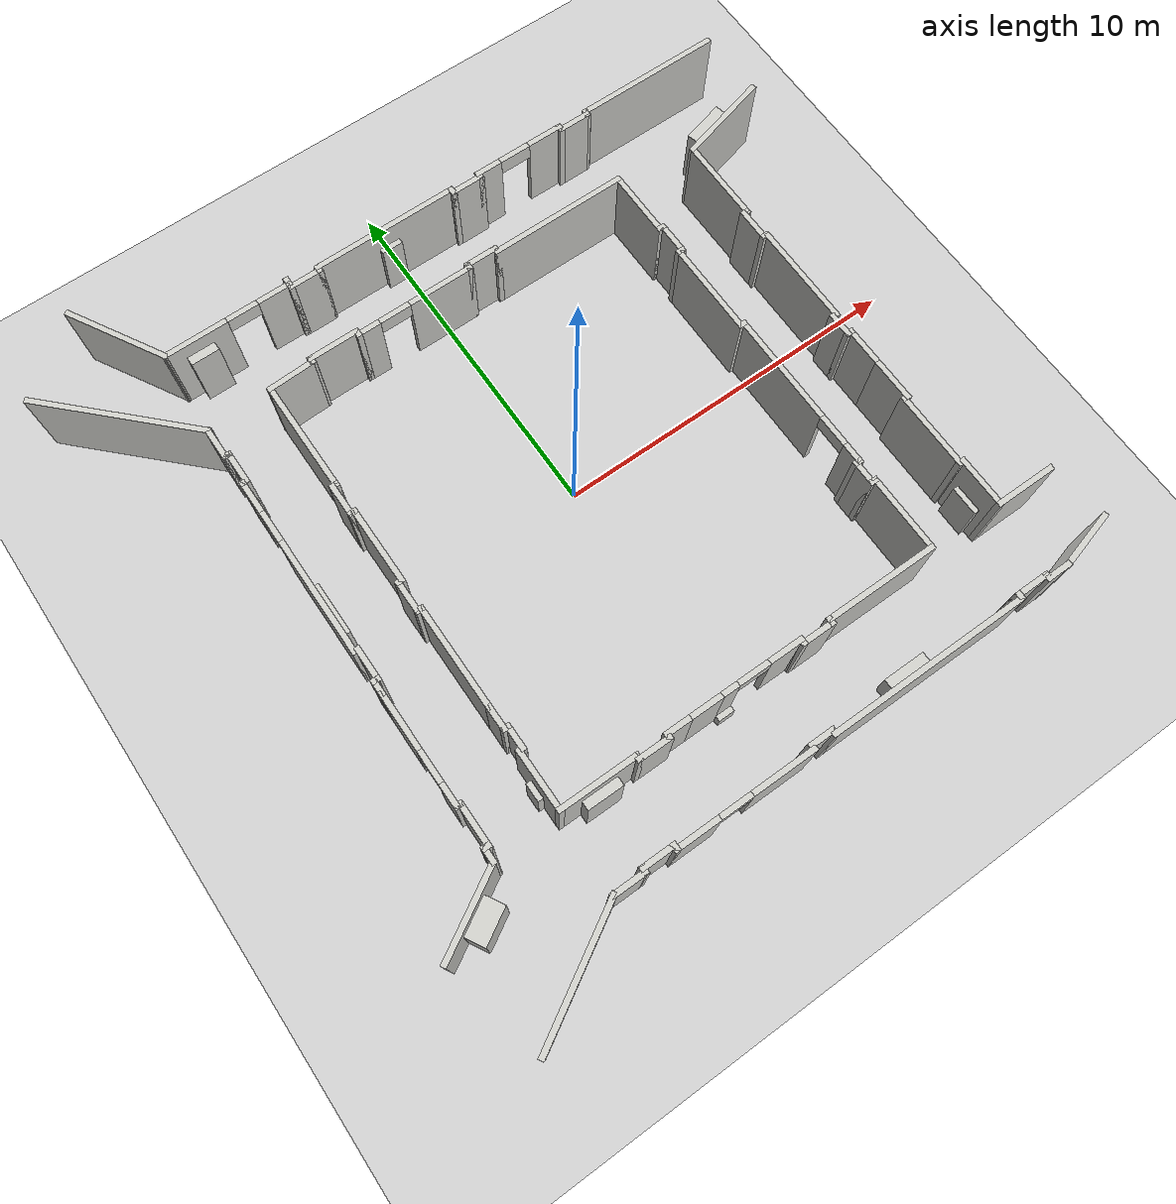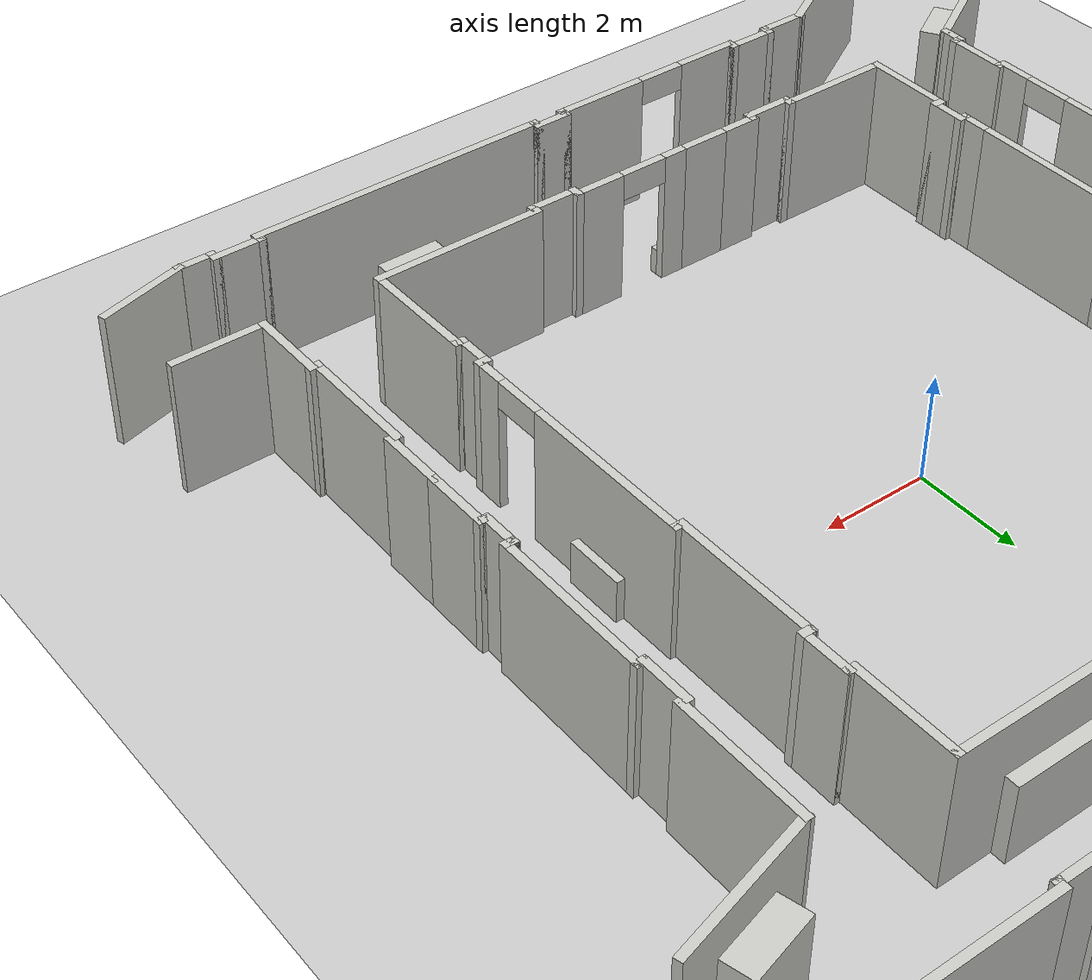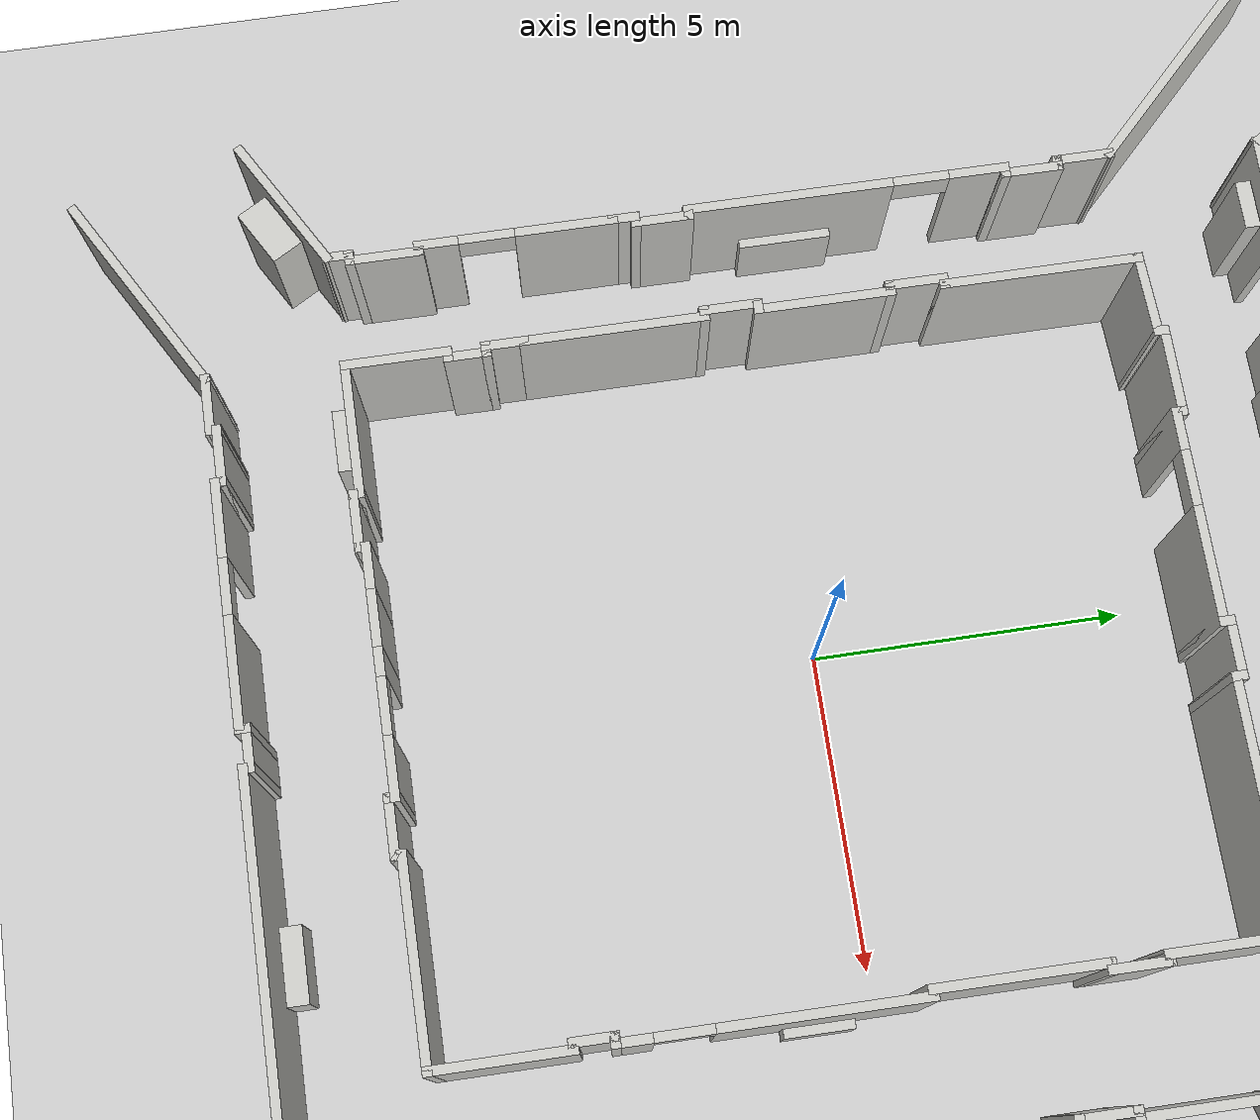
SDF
<sdf version="1.6">
 <world name="default">
  <light name="sun" type="directional">
   <pose>0 0 10 0 -0 0</pose>
   <diffuse>0.8 0.8 0.8 1</diffuse>
   <specular>0.1 0.1 0.1 1</specular>
   <attenuation>
    <range>1000</range>
    <constant>0.9</constant>
    <linear>0.01</linear>
    <quadratic>0.001</quadratic>
   </attenuation>
   <direction>-0.5 0.5 -1</direction>
  </light>
  <model name="ground_plane">
   <static>1</static>
   <link name="link">
    <collision name="collision">
     <geometry><plane><normal>0 0 1</normal><size>100 100</size></plane></geometry>
     <surface><friction><ode><mu>100</mu><mu2>50</mu2></ode></friction></surface>
    </collision>
    <visual name="visual">
     <cast_shadows>0</cast_shadows>
     <geometry><plane><normal>0 0 1</normal><size>100 100</size></plane></geometry>
     <material>
      <script><uri>file://media/materials/scripts/gazebo.material</uri><name>Gazebo/Grey</name></script>
     </material>
    </visual>
   </link>
  </model>
  <gravity>0 0 -9.8</gravity>
  <magnetic_field>6e-06 2.3e-05 -4.2e-05</magnetic_field>
  <atmosphere type="adiabatic"/>
  <physics name="default_physics" default="0" type="ode">
   <max_step_size>0.001</max_step_size>
   <real_time_factor>1</real_time_factor>
   <real_time_update_rate>1000</real_time_update_rate>
  </physics>
  <scene><ambient>0.4 0.4 0.4 1</ambient><background>0.7 0.7 0.7 1</background><shadows>1</shadows></scene>
  <spherical_coordinates>
   <surface_model>EARTH_WGS84</surface_model>
   <latitude_deg>0</latitude_deg>
   <longitude_deg>0</longitude_deg>
   <elevation>0</elevation>
   <heading_deg>0</heading_deg>
  </spherical_coordinates>
  <model name="mcbryde5">
   <pose>0.000403 -0.034137 0 0 -0 0</pose>
   <link name="Wall_102">
    <collision name="Wall_102_Collision">
     <geometry><box><size>0.15 0.15 2.5</size></box></geometry>
     <pose>0 0 1.25 0 -0 0</pose>
    </collision>
    <visual name="Wall_102_Visual">
     <pose>0 0 1.25 0 -0 0</pose>
     <geometry><box><size>0.15 0.15 2.5</size></box></geometry>
     <material>
      <script><uri>file://media/materials/scripts/gazebo.material</uri><name>Gazebo/CeilingTiled</name></script>
      <ambient>1 1 1 1</ambient>
     </material>
    </visual>
    <pose>-6.94903 4.93922 0 0 -0 0</pose>
   </link>
   <link name="Wall_103">
    <collision name="Wall_103_Collision">
     <geometry><box><size>0.25 0.15 2.5</size></box></geometry>
     <pose>0 0 1.25 0 -0 0</pose>
    </collision>
    <visual name="Wall_103_Visual">
     <pose>0 0 1.25 0 -0 0</pose>
     <geometry><box><size>0.25 0.15 2.5</size></box></geometry>
     <material>
      <script><uri>file://media/materials/scripts/gazebo.material</uri><name>Gazebo/CeilingTiled</name></script>
      <ambient>1 1 1 1</ambient>
     </material>
    </visual>
    <pose>-6.89903 4.93922 0 0 -0 0</pose>
   </link>
   <link name="Wall_104">
    <collision name="Wall_104_Collision">
     <geometry><box><size>1 0.15 2.5</size></box></geometry>
     <pose>0 0 1.25 0 -0 0</pose>
    </collision>
    <visual name="Wall_104_Visual">
     <pose>0 0 1.25 0 -0 0</pose>
     <geometry><box><size>1 0.15 2.5</size></box></geometry>
     <material>
      <script><uri>file://media/materials/scripts/gazebo.material</uri><name>Gazebo/CeilingTiled</name></script>
      <ambient>1 1 1 1</ambient>
     </material>
    </visual>
    <pose>-6.84903 4.51422 0 0 0 -1.5708</pose>
   </link>
   <link name="Wall_105">
    <collision name="Wall_105_Collision">
     <geometry><box><size>0.25 0.15 2.5</size></box></geometry>
     <pose>0 0 1.25 0 -0 0</pose>
    </collision>
    <visual name="Wall_105_Visual">
     <pose>0 0 1.25 0 -0 0</pose>
     <geometry><box><size>0.25 0.15 2.5</size></box></geometry>
     <material>
      <script><uri>file://media/materials/scripts/gazebo.material</uri><name>Gazebo/CeilingTiled</name></script>
      <ambient>1 1 1 1</ambient>
     </material>
    </visual>
    <pose>-6.89903 4.08922 0 0 -0 3.14159</pose>
   </link>
   <link name="Wall_106">
    <pose>-6.94903 1.53922 0 0 0 -1.5708</pose>
    <visual name="Wall_106_Visual_0">
     <pose>-2.13764 0 1.25 0 -0 0</pose>
     <geometry><box><size>0.974722 0.15 2.5</size></box></geometry>
     <material>
      <script><uri>file://media/materials/scripts/gazebo.material</uri><name>Gazebo/CeilingTiled</name></script>
      <ambient>1 1 1 1</ambient>
     </material>
    </visual>
    <collision name="Wall_106_Collision_0">
     <geometry><box><size>0.974722 0.15 2.5</size></box></geometry>
     <pose>-2.13764 0 1.25 0 -0 0</pose>
    </collision>
    <visual name="Wall_106_Visual_1">
     <pose>0.937361 0 1.25 0 -0 0</pose>
     <geometry><box><size>3.37528 0.15 2.5</size></box></geometry>
     <material>
      <script><uri>file://media/materials/scripts/gazebo.material</uri><name>Gazebo/CeilingTiled</name></script>
      <ambient>1 1 1 1</ambient>
     </material>
    </visual>
    <collision name="Wall_106_Collision_1">
     <geometry><box><size>3.37528 0.15 2.5</size></box></geometry>
     <pose>0.937361 0 1.25 0 -0 0</pose>
    </collision>
    <visual name="Wall_106_Visual_2">
     <pose>-1.20028 0 2.25 0 -0 0</pose>
     <geometry><box><size>0.9 0.15 0.5</size></box></geometry>
     <material>
      <script><uri>file://media/materials/scripts/gazebo.material</uri><name>Gazebo/CeilingTiled</name></script>
      <ambient>1 1 1 1</ambient>
     </material>
    </visual>
    <collision name="Wall_106_Collision_2">
     <geometry><box><size>0.9 0.15 0.5</size></box></geometry>
     <pose>-1.20028 0 2.25 0 -0 0</pose>
    </collision>
    <visual name="Wall_106_Visual_3">
     <pose>0.937361 0.15 0.6 0 -0 0</pose>
     <geometry><box><size>1.5 0.15 1.2</size></box></geometry>
     <material>
      <script><uri>file://media/materials/scripts/gazebo.material</uri><name>Gazebo/CeilingTiled</name></script>
      <ambient>0.6 0.6 1 1</ambient>
     </material>
    </visual>
    <collision name="Wall_106_Collision_3">
     <geometry><box><size>1.5 0.15 1.2</size></box></geometry>
     <pose>0.937361 0.15 0.6 0 -0 0</pose>
    </collision>
   </link>
   <link name="Wall_107">
    <collision name="Wall_107_Collision">
     <geometry><box><size>0.25 0.15 2.5</size></box></geometry>
     <pose>0 0 1.25 0 -0 0</pose>
    </collision>
    <visual name="Wall_107_Visual">
     <pose>0 0 1.25 0 -0 0</pose>
     <geometry><box><size>0.25 0.15 2.5</size></box></geometry>
     <material>
      <script><uri>file://media/materials/scripts/gazebo.material</uri><name>Gazebo/CeilingTiled</name></script>
      <ambient>1 1 1 1</ambient>
     </material>
    </visual>
    <pose>-6.89903 -1.01078 0 0 -0 0</pose>
   </link>
   <link name="Wall_108">
    <collision name="Wall_108_Collision">
     <geometry><box><size>1 0.15 2.5</size></box></geometry>
     <pose>0 0 1.25 0 -0 0</pose>
    </collision>
    <visual name="Wall_108_Visual">
     <pose>0 0 1.25 0 -0 0</pose>
     <geometry><box><size>1 0.15 2.5</size></box></geometry>
     <material>
      <script><uri>file://media/materials/scripts/gazebo.material</uri><name>Gazebo/CeilingTiled</name></script>
      <ambient>1 1 1 1</ambient>
     </material>
    </visual>
    <pose>-6.84903 -1.43578 0 0 0 -1.5708</pose>
   </link>
   <link name="Wall_109">
    <collision name="Wall_109_Collision">
     <geometry><box><size>0.25 0.15 2.5</size></box></geometry>
     <pose>0 0 1.25 0 -0 0</pose>
    </collision>
    <visual name="Wall_109_Visual">
     <pose>0 0 1.25 0 -0 0</pose>
     <geometry><box><size>0.25 0.15 2.5</size></box></geometry>
     <material>
      <script><uri>file://media/materials/scripts/gazebo.material</uri><name>Gazebo/CeilingTiled</name></script>
      <ambient>1 1 1 1</ambient>
     </material>
    </visual>
    <pose>-6.89903 -1.86078 0 0 -0 3.14159</pose>
   </link>
   <link name="Wall_110">
    <collision name="Wall_110_Collision">
     <geometry><box><size>0.5 0.15 2.5</size></box></geometry>
     <pose>0 0 1.25 0 -0 0</pose>
    </collision>
    <visual name="Wall_110_Visual">
     <pose>0 0 1.25 0 -0 0</pose>
     <geometry><box><size>0.5 0.15 2.5</size></box></geometry>
     <material>
      <script><uri>file://media/materials/scripts/gazebo.material</uri><name>Gazebo/CeilingTiled</name></script>
      <ambient>1 1 1 1</ambient>
     </material>
    </visual>
    <pose>-6.94903 -2.03578 0 0 0 -1.5708</pose>
   </link>
   <link name="Wall_112">
    <pose>-6.94903 -3.76078 0 0 0 -1.5708</pose>
    <visual name="Wall_112_Visual_0">
     <pose>-0.803013 0 1.25 0 -0 0</pose>
     <geometry><box><size>1.64397 0.15 2.5</size></box></geometry>
     <material>
      <script><uri>file://media/materials/scripts/gazebo.material</uri><name>Gazebo/CeilingTiled</name></script>
      <ambient>1 1 1 1</ambient>
     </material>
    </visual>
    <collision name="Wall_112_Collision_0">
     <geometry><box><size>1.64397 0.15 2.5</size></box></geometry>
     <pose>-0.803013 0 1.25 0 -0 0</pose>
    </collision>
    <visual name="Wall_112_Visual_1">
     <pose>1.27199 0 1.25 0 -0 0</pose>
     <geometry><box><size>0.706025 0.15 2.5</size></box></geometry>
     <material>
      <script><uri>file://media/materials/scripts/gazebo.material</uri><name>Gazebo/CeilingTiled</name></script>
      <ambient>1 1 1 1</ambient>
     </material>
    </visual>
    <collision name="Wall_112_Collision_1">
     <geometry><box><size>0.706025 0.15 2.5</size></box></geometry>
     <pose>1.27199 0 1.25 0 -0 0</pose>
    </collision>
    <visual name="Wall_112_Visual_2">
     <pose>0.468975 0 2.25 0 -0 0</pose>
     <geometry><box><size>0.9 0.15 0.5</size></box></geometry>
     <material>
      <script><uri>file://media/materials/scripts/gazebo.material</uri><name>Gazebo/CeilingTiled</name></script>
      <ambient>1 1 1 1</ambient>
     </material>
    </visual>
    <collision name="Wall_112_Collision_2">
     <geometry><box><size>0.9 0.15 0.5</size></box></geometry>
     <pose>0.468975 0 2.25 0 -0 0</pose>
    </collision>
   </link>
   <link name="Wall_113">
    <collision name="Wall_113_Collision">
     <geometry><box><size>0.25 0.15 2.5</size></box></geometry>
     <pose>0 0 1.25 0 -0 0</pose>
    </collision>
    <visual name="Wall_113_Visual">
     <pose>0 0 1.25 0 -0 0</pose>
     <geometry><box><size>0.25 0.15 2.5</size></box></geometry>
     <material>
      <script><uri>file://media/materials/scripts/gazebo.material</uri><name>Gazebo/CeilingTiled</name></script>
      <ambient>1 1 1 1</ambient>
     </material>
    </visual>
    <pose>-6.89903 -5.31078 0 0 -0 0</pose>
   </link>
   <link name="Wall_114">
    <collision name="Wall_114_Collision">
     <geometry><box><size>1.25 0.15 2.5</size></box></geometry>
     <pose>0 0 1.25 0 -0 0</pose>
    </collision>
    <visual name="Wall_114_Visual">
     <pose>0 0 1.25 0 -0 0</pose>
     <geometry><box><size>1.25 0.15 2.5</size></box></geometry>
     <material>
      <script><uri>file://media/materials/scripts/gazebo.material</uri><name>Gazebo/CeilingTiled</name></script>
      <ambient>1 1 1 1</ambient>
     </material>
    </visual>
    <pose>-6.84903 -5.86078 0 0 0 -1.5708</pose>
   </link>
   <link name="Wall_115">
    <collision name="Wall_115_Collision">
     <geometry><box><size>0.25 0.15 2.5</size></box></geometry>
     <pose>0 0 1.25 0 -0 0</pose>
    </collision>
    <visual name="Wall_115_Visual">
     <pose>0 0 1.25 0 -0 0</pose>
     <geometry><box><size>0.25 0.15 2.5</size></box></geometry>
     <material>
      <script><uri>file://media/materials/scripts/gazebo.material</uri><name>Gazebo/CeilingTiled</name></script>
      <ambient>1 1 1 1</ambient>
     </material>
    </visual>
    <pose>-6.89903 -6.41078 0 0 -0 3.14159</pose>
   </link>
   <link name="Wall_116">
    <collision name="Wall_116_Collision">
     <geometry><box><size>0.5 0.15 2.5</size></box></geometry>
     <pose>0 0 1.25 0 -0 0</pose>
    </collision>
    <visual name="Wall_116_Visual">
     <pose>0 0 1.25 0 -0 0</pose>
     <geometry><box><size>0.5 0.15 2.5</size></box></geometry>
     <material>
      <script><uri>file://media/materials/scripts/gazebo.material</uri><name>Gazebo/CeilingTiled</name></script>
      <ambient>1 1 1 1</ambient>
     </material>
    </visual>
    <pose>-6.94903 -6.58578 0 0 0 -1.5708</pose>
   </link>
   <link name="Wall_117">
    <collision name="Wall_117_Collision_0">
     <geometry><box><size>2.5 0.15 2.5</size></box></geometry>
     <pose>0 0 1.25 0 -0 0</pose>
    </collision>
    <visual name="Wall_117_Visual_0">
     <pose>0 0 1.25 0 -0 0</pose>
     <geometry><box><size>2.5 0.15 2.5</size></box></geometry>
     <material>
      <script><uri>file://media/materials/scripts/gazebo.material</uri><name>Gazebo/CeilingTiled</name></script>
      <ambient>1 1 1 1</ambient>
     </material>
    </visual>
    <collision name="Wall_117_Collision_1">
     <geometry><box><size>1.0 0.55 2.0</size></box></geometry>
     <pose>0 0.35 1.0 0 -0 0</pose>
    </collision>
    <visual name="Wall_117_Visual_1">
     <pose>0 0.35 1.0 0 -0 0</pose>
     <geometry><box><size>1.0 0.55 2.0</size></box></geometry>
     <material>
      <script><uri>file://media/materials/scripts/gazebo.material</uri><name>Gazebo/CeilingTiled</name></script>
      <ambient>0.3 1 0.3 1</ambient>
     </material>
    </visual>
    <pose>-7.96661 -7.34828 0 0 0 -2.61799</pose>
   </link>
   <link name="Wall_119">
    <collision name="Wall_119_Collision">
     <geometry><box><size>3.75 0.15 2.5</size></box></geometry>
     <pose>0 0 1.25 0 -0 0</pose>
    </collision>
    <visual name="Wall_119_Visual">
     <pose>0 0 1.25 0 -0 0</pose>
     <geometry><box><size>3.75 0.15 2.5</size></box></geometry>
     <material>
      <script><uri>file://media/materials/scripts/gazebo.material</uri><name>Gazebo/CeilingTiled</name></script>
      <ambient>1 1 1 1</ambient>
     </material>
    </visual>
    <pose>-6.76357 -9.73795 0 0 -0 0.523599</pose>
   </link>
   <link name="Wall_120">
    <collision name="Wall_120_Collision">
     <geometry><box><size>1 0.15 2.5</size></box></geometry>
     <pose>0 0 1.25 0 -0 0</pose>
    </collision>
    <visual name="Wall_120_Visual">
     <pose>0 0 1.25 0 -0 0</pose>
     <geometry><box><size>1 0.15 2.5</size></box></geometry>
     <material>
      <script><uri>file://media/materials/scripts/gazebo.material</uri><name>Gazebo/CeilingTiled</name></script>
      <ambient>1 1 1 1</ambient>
     </material>
    </visual>
    <pose>-4.77972 -8.83795 0 0 -0 0</pose>
   </link>
   <link name="Wall_121">
    <collision name="Wall_121_Collision">
     <geometry><box><size>0.25 0.15 2.5</size></box></geometry>
     <pose>0 0 1.25 0 -0 0</pose>
    </collision>
    <visual name="Wall_121_Visual">
     <pose>0 0 1.25 0 -0 0</pose>
     <geometry><box><size>0.25 0.15 2.5</size></box></geometry>
     <material>
      <script><uri>file://media/materials/scripts/gazebo.material</uri><name>Gazebo/CeilingTiled</name></script>
      <ambient>1 1 1 1</ambient>
     </material>
    </visual>
    <pose>-4.35472 -8.78795 0 0 -0 1.5708</pose>
   </link>
   <link name="Wall_122">
    <collision name="Wall_122_Collision">
     <geometry><box><size>1 0.15 2.5</size></box></geometry>
     <pose>0 0 1.25 0 -0 0</pose>
    </collision>
    <visual name="Wall_122_Visual">
     <pose>0 0 1.25 0 -0 0</pose>
     <geometry><box><size>1 0.15 2.5</size></box></geometry>
     <material>
      <script><uri>file://media/materials/scripts/gazebo.material</uri><name>Gazebo/CeilingTiled</name></script>
      <ambient>1 1 1 1</ambient>
     </material>
    </visual>
    <pose>-3.92972 -8.73795 0 0 -0 0</pose>
   </link>
   <link name="Wall_123">
    <collision name="Wall_123_Collision">
     <geometry><box><size>0.25 0.15 2.5</size></box></geometry>
     <pose>0 0 1.25 0 -0 0</pose>
    </collision>
    <visual name="Wall_123_Visual">
     <pose>0 0 1.25 0 -0 0</pose>
     <geometry><box><size>0.25 0.15 2.5</size></box></geometry>
     <material>
      <script><uri>file://media/materials/scripts/gazebo.material</uri><name>Gazebo/CeilingTiled</name></script>
      <ambient>1 1 1 1</ambient>
     </material>
    </visual>
    <pose>-3.50472 -8.78795 0 0 0 -1.5708</pose>
   </link>
   <link name="Wall_124">
    <pose>-1.57972 -8.83795 0 0 -0 0</pose>
    <visual name="Wall_124_Visual_0">
     <pose>-1.36383 0 1.25 0 -0 0</pose>
     <geometry><box><size>1.27234 0.15 2.5</size></box></geometry>
     <material>
      <script><uri>file://media/materials/scripts/gazebo.material</uri><name>Gazebo/CeilingTiled</name></script>
      <ambient>1 1 1 1</ambient>
     </material>
    </visual>
    <collision name="Wall_124_Collision_0">
     <geometry><box><size>1.27234 0.15 2.5</size></box></geometry>
     <pose>-1.36383 0 1.25 0 -0 0</pose>
    </collision>
    <visual name="Wall_124_Visual_1">
     <pose>1.08617 0 1.25 0 -0 0</pose>
     <geometry><box><size>1.82766 0.15 2.5</size></box></geometry>
     <material>
      <script><uri>file://media/materials/scripts/gazebo.material</uri><name>Gazebo/CeilingTiled</name></script>
      <ambient>1 1 1 1</ambient>
     </material>
    </visual>
    <collision name="Wall_124_Collision_1">
     <geometry><box><size>1.82766 0.15 2.5</size></box></geometry>
     <pose>1.08617 0 1.25 0 -0 0</pose>
    </collision>
    <visual name="Wall_124_Visual_2">
     <pose>-0.277656 0 2.25 0 -0 0</pose>
     <geometry><box><size>0.9 0.15 0.5</size></box></geometry>
     <material>
      <script><uri>file://media/materials/scripts/gazebo.material</uri><name>Gazebo/CeilingTiled</name></script>
      <ambient>1 1 1 1</ambient>
     </material>
    </visual>
    <collision name="Wall_124_Collision_2">
     <geometry><box><size>0.9 0.15 0.5</size></box></geometry>
     <pose>-0.277656 0 2.25 0 -0 0</pose>
    </collision>
   </link>
   <link name="Wall_125">
    <collision name="Wall_125_Collision">
     <geometry><box><size>0.25 0.15 2.5</size></box></geometry>
     <pose>0 0 1.25 0 -0 0</pose>
    </collision>
    <visual name="Wall_125_Visual">
     <pose>0 0 1.25 0 -0 0</pose>
     <geometry><box><size>0.25 0.15 2.5</size></box></geometry>
     <material>
      <script><uri>file://media/materials/scripts/gazebo.material</uri><name>Gazebo/CeilingTiled</name></script>
      <ambient>1 1 1 1</ambient>
     </material>
    </visual>
    <pose>0.345276 -8.78795 0 0 -0 1.5708</pose>
   </link>
   <link name="Wall_126">
    <collision name="Wall_126_Collision">
     <geometry><box><size>0.75 0.15 2.5</size></box></geometry>
     <pose>0 0 1.25 0 -0 0</pose>
    </collision>
    <visual name="Wall_126_Visual">
     <pose>0 0 1.25 0 -0 0</pose>
     <geometry><box><size>0.75 0.15 2.5</size></box></geometry>
     <material>
      <script><uri>file://media/materials/scripts/gazebo.material</uri><name>Gazebo/CeilingTiled</name></script>
      <ambient>1 1 1 1</ambient>
     </material>
    </visual>
    <pose>0.645276 -8.73795 0 0 -0 0</pose>
   </link>
   <link name="Wall_127">
    <collision name="Wall_127_Collision">
     <geometry><box><size>0.25 0.15 2.5</size></box></geometry>
     <pose>0 0 1.25 0 -0 0</pose>
    </collision>
    <visual name="Wall_127_Visual">
     <pose>0 0 1.25 0 -0 0</pose>
     <geometry><box><size>0.25 0.15 2.5</size></box></geometry>
     <material>
      <script><uri>file://media/materials/scripts/gazebo.material</uri><name>Gazebo/CeilingTiled</name></script>
      <ambient>1 1 1 1</ambient>
     </material>
    </visual>
    <pose>0.945276 -8.78795 0 0 0 -1.5708</pose>
   </link>
   <link name="Wall_128">
    <collision name="Wall_128_Collision_0">
     <geometry><box><size>5.75 0.15 2.5</size></box></geometry>
     <pose>0 0 1.25 0 -0 0</pose>
    </collision>
    <visual name="Wall_128_Visual_0">
     <pose>0 0 1.25 0 -0 0</pose>
     <geometry><box><size>5.75 0.15 2.5</size></box></geometry>
     <material>
      <script><uri>file://media/materials/scripts/gazebo.material</uri><name>Gazebo/CeilingTiled</name></script>
      <ambient>1 1 1 1</ambient>
     </material>
    </visual>
    <collision name="Wall_128_Collision_1">
     <geometry><box><size>1.2 0.35 1.0</size></box></geometry>
     <pose>0 0.25 0.5 0 -0 0</pose>
    </collision>
    <visual name="Wall_128_Visual_1">
     <pose>0 0.25 0.5 0 -0 0</pose>
     <geometry><box><size>1.2 0.35 1.0</size></box></geometry>
     <material>
      <script><uri>file://media/materials/scripts/gazebo.material</uri><name>Gazebo/CeilingTiled</name></script>
      <ambient>0.4 0.4 1 1</ambient>
     </material>
    </visual>
    <pose>3.74528 -8.83795 0 0 -0 0</pose>
   </link>
   <link name="Wall_129">
    <collision name="Wall_129_Collision">
     <geometry><box><size>0.25 0.15 2.5</size></box></geometry>
     <pose>0 0 1.25 0 -0 0</pose>
    </collision>
    <visual name="Wall_129_Visual">
     <pose>0 0 1.25 0 -0 0</pose>
     <geometry><box><size>0.25 0.15 2.5</size></box></geometry>
     <material>
      <script><uri>file://media/materials/scripts/gazebo.material</uri><name>Gazebo/CeilingTiled</name></script>
      <ambient>1 1 1 1</ambient>
     </material>
    </visual>
    <pose>6.54528 -8.78795 0 0 -0 1.5708</pose>
   </link>
   <link name="Wall_130">
    <collision name="Wall_130_Collision">
     <geometry><box><size>1 0.15 2.5</size></box></geometry>
     <pose>0 0 1.25 0 -0 0</pose>
    </collision>
    <visual name="Wall_130_Visual">
     <pose>0 0 1.25 0 -0 0</pose>
     <geometry><box><size>1 0.15 2.5</size></box></geometry>
     <material>
      <script><uri>file://media/materials/scripts/gazebo.material</uri><name>Gazebo/CeilingTiled</name></script>
      <ambient>1 1 1 1</ambient>
     </material>
    </visual>
    <pose>6.97028 -8.73795 0 0 -0 0</pose>
   </link>
   <link name="Wall_131">
    <collision name="Wall_131_Collision">
     <geometry><box><size>0.25 0.15 2.5</size></box></geometry>
     <pose>0 0 1.25 0 -0 0</pose>
    </collision>
    <visual name="Wall_131_Visual">
     <pose>0 0 1.25 0 -0 0</pose>
     <geometry><box><size>0.25 0.15 2.5</size></box></geometry>
     <material>
      <script><uri>file://media/materials/scripts/gazebo.material</uri><name>Gazebo/CeilingTiled</name></script>
      <ambient>1 1 1 1</ambient>
     </material>
    </visual>
    <pose>7.39528 -8.78795 0 0 0 -1.5708</pose>
   </link>
   <link name="Wall_132">
    <collision name="Wall_132_Collision">
     <geometry><box><size>0.75 0.15 2.5</size></box></geometry>
     <pose>0 0 1.25 0 -0 0</pose>
    </collision>
    <visual name="Wall_132_Visual">
     <pose>0 0 1.25 0 -0 0</pose>
     <geometry><box><size>0.75 0.15 2.5</size></box></geometry>
     <material>
      <script><uri>file://media/materials/scripts/gazebo.material</uri><name>Gazebo/CeilingTiled</name></script>
      <ambient>1 1 1 1</ambient>
     </material>
    </visual>
    <pose>7.69528 -8.83795 0 0 -0 0</pose>
   </link>
   <link name="Wall_133">
    <collision name="Wall_133_Collision">
     <geometry><box><size>1.75 0.15 2.5</size></box></geometry>
     <pose>0 0 1.25 0 -0 0</pose>
    </collision>
    <visual name="Wall_133_Visual">
     <pose>0 0 1.25 0 -0 0</pose>
     <geometry><box><size>1.75 0.15 2.5</size></box></geometry>
     <material>
      <script><uri>file://media/materials/scripts/gazebo.material</uri><name>Gazebo/CeilingTiled</name></script>
      <ambient>1 1 1 1</ambient>
     </material>
    </visual>
    <pose>8.76802 -8.6309 0 0 -0 0.261799</pose>
   </link>
   <link name="Wall_136">
    <collision name="Wall_136_Collision">
     <geometry><box><size>1.75 0.15 2.5</size></box></geometry>
     <pose>0 0 1.25 0 -0 0</pose>
    </collision>
    <visual name="Wall_136_Visual">
     <pose>0 0 1.25 0 -0 0</pose>
     <geometry><box><size>1.75 0.15 2.5</size></box></geometry>
     <material>
      <script><uri>file://media/materials/scripts/gazebo.material</uri><name>Gazebo/CeilingTiled</name></script>
      <ambient>1 1 1 1</ambient>
     </material>
    </visual>
    <pose>8.50453 -6.75972 0 0 -0 3.14159</pose>
   </link>
   <link name="Wall_137">
    <collision name="Wall_137_Collision_0">
     <geometry><box><size>1.5 0.15 2.5</size></box></geometry>
     <pose>0 0 1.25 0 -0 0</pose>
    </collision>
    <visual name="Wall_137_Visual_0">
     <pose>0 0 1.25 0 -0 0</pose>
     <geometry><box><size>1.5 0.15 2.5</size></box></geometry>
     <material>
      <script><uri>file://media/materials/scripts/gazebo.material</uri><name>Gazebo/CeilingTiled</name></script>
      <ambient>1 1 1 1</ambient>
     </material>
    </visual>
    <collision name="Wall_137_Collision_1">
     <geometry><box><size>0.8 0.15 1.5</size></box></geometry>
     <pose>0 0.15 0.75 0 -0 0</pose>
    </collision>
    <visual name="Wall_137_Visual_1">
     <pose>0 0.15 0.75 0 -0 0</pose>
     <geometry><box><size>0.8 0.15 1.5</size></box></geometry>
     <material>
      <script><uri>file://media/materials/scripts/gazebo.material</uri><name>Gazebo/CeilingTiled</name></script>
      <ambient>1 0.6 1 1</ambient>
     </material>
    </visual>
    <pose>7.70453 -6.08472 0 0 -0 1.5708</pose>
   </link>
   <link name="Wall_138">
    <collision name="Wall_138_Collision">
     <geometry><box><size>0.25 0.15 2.5</size></box></geometry>
     <pose>0 0 1.25 0 -0 0</pose>
    </collision>
    <visual name="Wall_138_Visual">
     <pose>0 0 1.25 0 -0 0</pose>
     <geometry><box><size>0.25 0.15 2.5</size></box></geometry>
     <material>
      <script><uri>file://media/materials/scripts/gazebo.material</uri><name>Gazebo/CeilingTiled</name></script>
      <ambient>1 1 1 1</ambient>
     </material>
    </visual>
    <pose>7.65453 -5.40972 0 0 -0 3.14159</pose>
   </link>
   <link name="Wall_139">
    <collision name="Wall_139_Collision">
     <geometry><box><size>2.25 0.15 2.5</size></box></geometry>
     <pose>0 0 1.25 0 -0 0</pose>
    </collision>
    <visual name="Wall_139_Visual">
     <pose>0 0 1.25 0 -0 0</pose>
     <geometry><box><size>2.25 0.15 2.5</size></box></geometry>
     <material>
      <script><uri>file://media/materials/scripts/gazebo.material</uri><name>Gazebo/CeilingTiled</name></script>
      <ambient>1 1 1 1</ambient>
     </material>
    </visual>
    <pose>7.60453 -4.35972 0 0 -0 1.5708</pose>
   </link>
   <link name="Wall_14">
    <collision name="Wall_14_Collision">
     <geometry><box><size>0.15 0.15 2.5</size></box></geometry>
     <pose>0 0 1.25 0 -0 0</pose>
    </collision>
    <visual name="Wall_14_Visual">
     <pose>0 0 1.25 0 -0 0</pose>
     <geometry><box><size>0.15 0.15 2.5</size></box></geometry>
     <material>
      <script><uri>file://media/materials/scripts/gazebo.material</uri><name>Gazebo/CeilingTiled</name></script>
      <ambient>1 1 1 1</ambient>
     </material>
    </visual>
    <pose>-3.20531 8.30498 0 0 -0 0</pose>
   </link>
   <link name="Wall_140">
    <collision name="Wall_140_Collision">
     <geometry><box><size>0.25 0.15 2.5</size></box></geometry>
     <pose>0 0 1.25 0 -0 0</pose>
    </collision>
    <visual name="Wall_140_Visual">
     <pose>0 0 1.25 0 -0 0</pose>
     <geometry><box><size>0.25 0.15 2.5</size></box></geometry>
     <material>
      <script><uri>file://media/materials/scripts/gazebo.material</uri><name>Gazebo/CeilingTiled</name></script>
      <ambient>1 1 1 1</ambient>
     </material>
    </visual>
    <pose>7.65453 -3.30972 0 0 -0 0</pose>
   </link>
   <link name="Wall_141">
    <collision name="Wall_141_Collision">
     <geometry><box><size>1.25 0.15 2.5</size></box></geometry>
     <pose>0 0 1.25 0 -0 0</pose>
    </collision>
    <visual name="Wall_141_Visual">
     <pose>0 0 1.25 0 -0 0</pose>
     <geometry><box><size>1.25 0.15 2.5</size></box></geometry>
     <material>
      <script><uri>file://media/materials/scripts/gazebo.material</uri><name>Gazebo/CeilingTiled</name></script>
      <ambient>1 1 1 1</ambient>
     </material>
    </visual>
    <pose>7.70453 -2.75972 0 0 -0 1.5708</pose>
   </link>
   <link name="Wall_143">
    <collision name="Wall_143_Collision">
     <geometry><box><size>1.25 0.15 2.5</size></box></geometry>
     <pose>0 0 1.25 0 -0 0</pose>
    </collision>
    <visual name="Wall_143_Visual">
     <pose>0 0 1.25 0 -0 0</pose>
     <geometry><box><size>1.25 0.15 2.5</size></box></geometry>
     <material>
      <script><uri>file://media/materials/scripts/gazebo.material</uri><name>Gazebo/CeilingTiled</name></script>
      <ambient>1 1 1 1</ambient>
     </material>
    </visual>
    <pose>7.70453 -1.65972 0 0 -0 1.5708</pose>
   </link>
   <link name="Wall_144">
    <collision name="Wall_144_Collision">
     <geometry><box><size>0.25 0.15 2.5</size></box></geometry>
     <pose>0 0 1.25 0 -0 0</pose>
    </collision>
    <visual name="Wall_144_Visual">
     <pose>0 0 1.25 0 -0 0</pose>
     <geometry><box><size>0.25 0.15 2.5</size></box></geometry>
     <material>
      <script><uri>file://media/materials/scripts/gazebo.material</uri><name>Gazebo/CeilingTiled</name></script>
      <ambient>1 1 1 1</ambient>
     </material>
    </visual>
    <pose>7.65453 -1.10972 0 0 -0 3.14159</pose>
   </link>
   <link name="Wall_145">
    <collision name="Wall_145_Collision">
     <geometry><box><size>0.75 0.15 2.5</size></box></geometry>
     <pose>0 0 1.25 0 -0 0</pose>
    </collision>
    <visual name="Wall_145_Visual">
     <pose>0 0 1.25 0 -0 0</pose>
     <geometry><box><size>0.75 0.15 2.5</size></box></geometry>
     <material>
      <script><uri>file://media/materials/scripts/gazebo.material</uri><name>Gazebo/CeilingTiled</name></script>
      <ambient>1 1 1 1</ambient>
     </material>
    </visual>
    <pose>7.60453 -0.809722 0 0 -0 1.5708</pose>
   </link>
   <link name="Wall_146">
    <collision name="Wall_146_Collision">
     <geometry><box><size>0.25 0.15 2.5</size></box></geometry>
     <pose>0 0 1.25 0 -0 0</pose>
    </collision>
    <visual name="Wall_146_Visual">
     <pose>0 0 1.25 0 -0 0</pose>
     <geometry><box><size>0.25 0.15 2.5</size></box></geometry>
     <material>
      <script><uri>file://media/materials/scripts/gazebo.material</uri><name>Gazebo/CeilingTiled</name></script>
      <ambient>1 1 1 1</ambient>
     </material>
    </visual>
    <pose>7.65453 -0.509722 0 0 -0 0</pose>
   </link>
   <link name="Wall_147">
    <collision name="Wall_147_Collision">
     <geometry><box><size>3 0.15 2.5</size></box></geometry>
     <pose>0 0 1.25 0 -0 0</pose>
    </collision>
    <visual name="Wall_147_Visual">
     <pose>0 0 1.25 0 -0 0</pose>
     <geometry><box><size>3 0.15 2.5</size></box></geometry>
     <material>
      <script><uri>file://media/materials/scripts/gazebo.material</uri><name>Gazebo/CeilingTiled</name></script>
      <ambient>1 1 1 1</ambient>
     </material>
    </visual>
    <pose>7.70453 0.915278 0 0 -0 1.5708</pose>
   </link>
   <link name="Wall_149">
    <collision name="Wall_149_Collision">
     <geometry><box><size>0.25 0.15 2.5</size></box></geometry>
     <pose>0 0 1.25 0 -0 0</pose>
    </collision>
    <visual name="Wall_149_Visual">
     <pose>0 0 1.25 0 -0 0</pose>
     <geometry><box><size>0.25 0.15 2.5</size></box></geometry>
     <material>
      <script><uri>file://media/materials/scripts/gazebo.material</uri><name>Gazebo/CeilingTiled</name></script>
      <ambient>1 1 1 1</ambient>
     </material>
    </visual>
    <pose>7.65453 2.34028 0 0 -0 3.14159</pose>
   </link>
   <link name="Wall_150">
    <collision name="Wall_150_Collision">
     <geometry><box><size>1 0.15 2.5</size></box></geometry>
     <pose>0 0 1.25 0 -0 0</pose>
    </collision>
    <visual name="Wall_150_Visual">
     <pose>0 0 1.25 0 -0 0</pose>
     <geometry><box><size>1 0.15 2.5</size></box></geometry>
     <material>
      <script><uri>file://media/materials/scripts/gazebo.material</uri><name>Gazebo/CeilingTiled</name></script>
      <ambient>1 1 1 1</ambient>
     </material>
    </visual>
    <pose>7.60453 2.76528 0 0 -0 1.5708</pose>
   </link>
   <link name="Wall_151">
    <collision name="Wall_151_Collision">
     <geometry><box><size>0.25 0.15 2.5</size></box></geometry>
     <pose>0 0 1.25 0 -0 0</pose>
    </collision>
    <visual name="Wall_151_Visual">
     <pose>0 0 1.25 0 -0 0</pose>
     <geometry><box><size>0.25 0.15 2.5</size></box></geometry>
     <material>
      <script><uri>file://media/materials/scripts/gazebo.material</uri><name>Gazebo/CeilingTiled</name></script>
      <ambient>1 1 1 1</ambient>
     </material>
    </visual>
    <pose>7.65453 3.19028 0 0 -0 0</pose>
   </link>
   <link name="Wall_152">
    <collision name="Wall_152_Collision">
     <geometry><box><size>2.5 0.15 2.5</size></box></geometry>
     <pose>0 0 1.25 0 -0 0</pose>
    </collision>
    <visual name="Wall_152_Visual">
     <pose>0 0 1.25 0 -0 0</pose>
     <geometry><box><size>2.5 0.15 2.5</size></box></geometry>
     <material>
      <script><uri>file://media/materials/scripts/gazebo.material</uri><name>Gazebo/CeilingTiled</name></script>
      <ambient>1 1 1 1</ambient>
     </material>
    </visual>
    <pose>7.70453 4.36528 0 0 -0 1.5708</pose>
   </link>
   <link name="Wall_153">
    <collision name="Wall_153_Collision_0">
     <geometry><box><size>2.75 0.15 2.5</size></box></geometry>
     <pose>0 0 1.25 0 -0 0</pose>
    </collision>
    <visual name="Wall_153_Visual_0">
     <pose>0 0 1.25 0 -0 0</pose>
     <geometry><box><size>2.75 0.15 2.5</size></box></geometry>
     <material>
      <script><uri>file://media/materials/scripts/gazebo.material</uri><name>Gazebo/CeilingTiled</name></script>
      <ambient>1 1 1 1</ambient>
     </material>
    </visual>
    <collision name="Wall_153_Collision_1">
     <geometry><box><size>1.25 0.55 1.8</size></box></geometry>
     <pose>0 0.35 0.9 0 -0 0</pose>
    </collision>
    <visual name="Wall_153_Visual_1">
     <pose>0 0.35 0.9 0 -0 0</pose>
     <geometry><box><size>1.25 0.55 1.8</size></box></geometry>
     <material>
      <script><uri>file://media/materials/scripts/gazebo.material</uri><name>Gazebo/CeilingTiled</name></script>
      <ambient>1 0.4 0.4 1</ambient>
     </material>
    </visual>
    <pose>8.96023 5.87674 0 0 -0 0.261799</pose>
   </link>
   <link name="Wall_19">
    <collision name="Wall_19_Collision">
     <geometry><box><size>3 0.15 2.5</size></box></geometry>
     <pose>0 0 1.25 0 -0 0</pose>
    </collision>
    <visual name="Wall_19_Visual">
     <pose>0 0 1.25 0 -0 0</pose>
     <geometry><box><size>3 0.15 2.5</size></box></geometry>
     <material>
      <script><uri>file://media/materials/scripts/gazebo.material</uri><name>Gazebo/CeilingTiled</name></script>
      <ambient>1 1 1 1</ambient>
     </material>
    </visual>
    <pose>-7.52502 9.40387 0 0 0 -1.0472</pose>
   </link>
   <link name="Wall_20">
    <pose>-5.01252 8.16978 0 0 -0 0</pose>
    <visual name="Wall_20_Visual_0">
     <pose>-0.956139 0 1.25 0 -0 0</pose>
     <geometry><box><size>1.83772 0.15 2.5</size></box></geometry>
     <material>
      <script><uri>file://media/materials/scripts/gazebo.material</uri><name>Gazebo/CeilingTiled</name></script>
      <ambient>1 1 1 1</ambient>
     </material>
    </visual>
    <collision name="Wall_20_Collision_0">
     <geometry><box><size>1.83772 0.15 2.5</size></box></geometry>
     <pose>-0.956139 0 1.25 0 -0 0</pose>
    </collision>
    <visual name="Wall_20_Visual_1">
     <pose>1.36886 0 1.25 0 -0 0</pose>
     <geometry><box><size>1.01228 0.15 2.5</size></box></geometry>
     <material>
      <script><uri>file://media/materials/scripts/gazebo.material</uri><name>Gazebo/CeilingTiled</name></script>
      <ambient>1 1 1 1</ambient>
     </material>
    </visual>
    <collision name="Wall_20_Collision_1">
     <geometry><box><size>1.01228 0.15 2.5</size></box></geometry>
     <pose>1.36886 0 1.25 0 -0 0</pose>
    </collision>
    <visual name="Wall_20_Visual_2">
     <pose>0.412722 0 2.25 0 -0 0</pose>
     <geometry><box><size>0.9 0.15 0.5</size></box></geometry>
     <material>
      <script><uri>file://media/materials/scripts/gazebo.material</uri><name>Gazebo/CeilingTiled</name></script>
      <ambient>1 1 1 1</ambient>
     </material>
    </visual>
    <collision name="Wall_20_Collision_2">
     <geometry><box><size>0.9 0.15 0.5</size></box></geometry>
     <pose>0.412722 0 2.25 0 -0 0</pose>
    </collision>
    <visual name="Wall_20_Visual_3">
     <pose>-0.956139 -0.2 1.0 0 -0 0</pose>
     <geometry><box><size>0.8 0.25 2.0</size></box></geometry>
     <material>
      <script><uri>file://media/materials/scripts/gazebo.material</uri><name>Gazebo/CeilingTiled</name></script>
      <ambient>1 1 0.2 1</ambient>
     </material>
    </visual>
    <collision name="Wall_20_Collision_3">
     <geometry><box><size>0.8 0.25 2.0</size></box></geometry>
     <pose>-0.956139 -0.2 1.0 0 -0 0</pose>
    </collision>
   </link>
   <link name="Wall_21">
    <collision name="Wall_21_Collision">
     <geometry><box><size>0.25 0.15 2.5</size></box></geometry>
     <pose>0 0 1.25 0 -0 0</pose>
    </collision>
    <visual name="Wall_21_Visual">
     <pose>0 0 1.25 0 -0 0</pose>
     <geometry><box><size>0.25 0.15 2.5</size></box></geometry>
     <material>
      <script><uri>file://media/materials/scripts/gazebo.material</uri><name>Gazebo/CeilingTiled</name></script>
      <ambient>1 1 1 1</ambient>
     </material>
    </visual>
    <pose>-3.21252 8.11978 0 0 0 -1.5708</pose>
   </link>
   <link name="Wall_22">
    <collision name="Wall_22_Collision">
     <geometry><box><size>1 0.15 2.5</size></box></geometry>
     <pose>0 0 1.25 0 -0 0</pose>
    </collision>
    <visual name="Wall_22_Visual">
     <pose>0 0 1.25 0 -0 0</pose>
     <geometry><box><size>1 0.15 2.5</size></box></geometry>
     <material>
      <script><uri>file://media/materials/scripts/gazebo.material</uri><name>Gazebo/CeilingTiled</name></script>
      <ambient>1 1 1 1</ambient>
     </material>
    </visual>
    <pose>-2.78752 8.06978 0 0 -0 0</pose>
   </link>
   <link name="Wall_23">
    <collision name="Wall_23_Collision">
     <geometry><box><size>0.25 0.15 2.5</size></box></geometry>
     <pose>0 0 1.25 0 -0 0</pose>
    </collision>
    <visual name="Wall_23_Visual">
     <pose>0 0 1.25 0 -0 0</pose>
     <geometry><box><size>0.25 0.15 2.5</size></box></geometry>
     <material>
      <script><uri>file://media/materials/scripts/gazebo.material</uri><name>Gazebo/CeilingTiled</name></script>
      <ambient>1 1 1 1</ambient>
     </material>
    </visual>
    <pose>-2.36252 8.11978 0 0 -0 1.5708</pose>
   </link>
   <link name="Wall_24">
    <collision name="Wall_24_Collision_0">
     <geometry><box><size>4.25 0.15 2.5</size></box></geometry>
     <pose>0 0 1.25 0 -0 0</pose>
    </collision>
    <visual name="Wall_24_Visual_0">
     <pose>0 0 1.25 0 -0 0</pose>
     <geometry><box><size>4.25 0.15 2.5</size></box></geometry>
     <material>
      <script><uri>file://media/materials/scripts/gazebo.material</uri><name>Gazebo/CeilingTiled</name></script>
      <ambient>1 1 1 1</ambient>
     </material>
    </visual>
    <collision name="Wall_24_Collision_1">
     <geometry><box><size>0.6 0.15 1.8</size></box></geometry>
     <pose>0 -0.15 0.9 0 -0 0</pose>
    </collision>
    <visual name="Wall_24_Visual_1">
     <pose>0 -0.15 0.9 0 -0 0</pose>
     <geometry><box><size>0.6 0.15 1.8</size></box></geometry>
     <material>
      <script><uri>file://media/materials/scripts/gazebo.material</uri><name>Gazebo/CeilingTiled</name></script>
      <ambient>0.5 1 0.8 1</ambient>
     </material>
    </visual>
    <pose>-0.312519 8.16978 0 0 -0 0</pose>
   </link>
   <link name="Wall_25">
    <collision name="Wall_25_Collision">
     <geometry><box><size>0.25 0.15 2.5</size></box></geometry>
     <pose>0 0 1.25 0 -0 0</pose>
    </collision>
    <visual name="Wall_25_Visual">
     <pose>0 0 1.25 0 -0 0</pose>
     <geometry><box><size>0.25 0.15 2.5</size></box></geometry>
     <material>
      <script><uri>file://media/materials/scripts/gazebo.material</uri><name>Gazebo/CeilingTiled</name></script>
      <ambient>1 1 1 1</ambient>
     </material>
    </visual>
    <pose>1.73748 8.11978 0 0 0 -1.5708</pose>
   </link>
   <link name="Wall_26">
    <collision name="Wall_26_Collision">
     <geometry><box><size>1 0.15 2.5</size></box></geometry>
     <pose>0 0 1.25 0 -0 0</pose>
    </collision>
    <visual name="Wall_26_Visual">
     <pose>0 0 1.25 0 -0 0</pose>
     <geometry><box><size>1 0.15 2.5</size></box></geometry>
     <material>
      <script><uri>file://media/materials/scripts/gazebo.material</uri><name>Gazebo/CeilingTiled</name></script>
      <ambient>1 1 1 1</ambient>
     </material>
    </visual>
    <pose>2.16248 8.06978 0 0 -0 0</pose>
   </link>
   <link name="Wall_27">
    <collision name="Wall_27_Collision">
     <geometry><box><size>0.25 0.15 2.5</size></box></geometry>
     <pose>0 0 1.25 0 -0 0</pose>
    </collision>
    <visual name="Wall_27_Visual">
     <pose>0 0 1.25 0 -0 0</pose>
     <geometry><box><size>0.25 0.15 2.5</size></box></geometry>
     <material>
      <script><uri>file://media/materials/scripts/gazebo.material</uri><name>Gazebo/CeilingTiled</name></script>
      <ambient>1 1 1 1</ambient>
     </material>
    </visual>
    <pose>2.58748 8.11978 0 0 -0 1.5708</pose>
   </link>
   <link name="Wall_28">
    <pose>3.88748 8.16978 0 0 -0 0</pose>
    <visual name="Wall_28_Visual_0">
     <pose>-0.988297 0 1.25 0 -0 0</pose>
     <geometry><box><size>0.773405 0.15 2.5</size></box></geometry>
     <material>
      <script><uri>file://media/materials/scripts/gazebo.material</uri><name>Gazebo/CeilingTiled</name></script>
      <ambient>1 1 1 1</ambient>
     </material>
    </visual>
    <collision name="Wall_28_Collision_0">
     <geometry><box><size>0.773405 0.15 2.5</size></box></geometry>
     <pose>-0.988297 0 1.25 0 -0 0</pose>
    </collision>
    <visual name="Wall_28_Visual_1">
     <pose>0.836703 0 1.25 0 -0 0</pose>
     <geometry><box><size>1.07659 0.15 2.5</size></box></geometry>
     <material>
      <script><uri>file://media/materials/scripts/gazebo.material</uri><name>Gazebo/CeilingTiled</name></script>
      <ambient>1 1 1 1</ambient>
     </material>
    </visual>
    <collision name="Wall_28_Collision_1">
     <geometry><box><size>1.07659 0.15 2.5</size></box></geometry>
     <pose>0.836703 0 1.25 0 -0 0</pose>
    </collision>
    <visual name="Wall_28_Visual_2">
     <pose>-0.151595 0 2.25 0 -0 0</pose>
     <geometry><box><size>0.9 0.15 0.5</size></box></geometry>
     <material>
      <script><uri>file://media/materials/scripts/gazebo.material</uri><name>Gazebo/CeilingTiled</name></script>
      <ambient>1 1 1 1</ambient>
     </material>
    </visual>
    <collision name="Wall_28_Collision_2">
     <geometry><box><size>0.9 0.15 0.5</size></box></geometry>
     <pose>-0.151595 0 2.25 0 -0 0</pose>
    </collision>
   </link>
   <link name="Wall_29">
    <collision name="Wall_29_Collision">
     <geometry><box><size>0.25 0.15 2.5</size></box></geometry>
     <pose>0 0 1.25 0 -0 0</pose>
    </collision>
    <visual name="Wall_29_Visual">
     <pose>0 0 1.25 0 -0 0</pose>
     <geometry><box><size>0.25 0.15 2.5</size></box></geometry>
     <material>
      <script><uri>file://media/materials/scripts/gazebo.material</uri><name>Gazebo/CeilingTiled</name></script>
      <ambient>1 1 1 1</ambient>
     </material>
    </visual>
    <pose>5.18748 8.11978 0 0 0 -1.5708</pose>
   </link>
   <link name="Wall_30">
    <collision name="Wall_30_Collision">
     <geometry><box><size>1 0.15 2.5</size></box></geometry>
     <pose>0 0 1.25 0 -0 0</pose>
    </collision>
    <visual name="Wall_30_Visual">
     <pose>0 0 1.25 0 -0 0</pose>
     <geometry><box><size>1 0.15 2.5</size></box></geometry>
     <material>
      <script><uri>file://media/materials/scripts/gazebo.material</uri><name>Gazebo/CeilingTiled</name></script>
      <ambient>1 1 1 1</ambient>
     </material>
    </visual>
    <pose>5.61248 8.06978 0 0 -0 0</pose>
   </link>
   <link name="Wall_31">
    <collision name="Wall_31_Collision">
     <geometry><box><size>0.227973 0.15 2.5</size></box></geometry>
     <pose>0 0 1.25 0 -0 0</pose>
    </collision>
    <visual name="Wall_31_Visual">
     <pose>0 0 1.25 0 -0 0</pose>
     <geometry><box><size>0.227973 0.15 2.5</size></box></geometry>
     <material>
      <script><uri>file://media/materials/scripts/gazebo.material</uri><name>Gazebo/CeilingTiled</name></script>
      <ambient>1 1 1 1</ambient>
     </material>
    </visual>
    <pose>6.0432 8.10835 0 0 -0 1.42361</pose>
   </link>
   <link name="Wall_32">
    <collision name="Wall_32_Collision">
     <geometry><box><size>4.25 0.15 2.5</size></box></geometry>
     <pose>0 0 1.25 0 -0 0</pose>
    </collision>
    <visual name="Wall_32_Visual">
     <pose>0 0 1.25 0 -0 0</pose>
     <geometry><box><size>4.25 0.15 2.5</size></box></geometry>
     <material>
      <script><uri>file://media/materials/scripts/gazebo.material</uri><name>Gazebo/CeilingTiled</name></script>
      <ambient>1 1 1 1</ambient>
     </material>
    </visual>
    <pose>8.09892 8.15835 0 0 -0 0</pose>
   </link>
   <link name="Wall_35">
    <collision name="Wall_35_Collision">
     <geometry><box><size>0.25 0.15 2.5</size></box></geometry>
     <pose>0 0 1.25 0 -0 0</pose>
    </collision>
    <visual name="Wall_35_Visual">
     <pose>0 0 1.25 0 -0 0</pose>
     <geometry><box><size>0.25 0.15 2.5</size></box></geometry>
     <material>
      <script><uri>file://media/materials/scripts/gazebo.material</uri><name>Gazebo/CeilingTiled</name></script>
      <ambient>1 1 1 1</ambient>
     </material>
    </visual>
    <pose>-3.86866 5.97671 0 0 -0 1.5708</pose>
   </link>
   <link name="Wall_36">
    <collision name="Wall_36_Collision">
     <geometry><box><size>1.5 0.15 2.5</size></box></geometry>
     <pose>0 0 1.25 0 -0 0</pose>
    </collision>
    <visual name="Wall_36_Visual">
     <pose>0 0 1.25 0 -0 0</pose>
     <geometry><box><size>1.5 0.15 2.5</size></box></geometry>
     <material>
      <script><uri>file://media/materials/scripts/gazebo.material</uri><name>Gazebo/CeilingTiled</name></script>
      <ambient>1 1 1 1</ambient>
     </material>
    </visual>
    <pose>-3.19366 6.02671 0 0 -0 0</pose>
   </link>
   <link name="Wall_37">
    <collision name="Wall_37_Collision">
     <geometry><box><size>0.25 0.15 2.5</size></box></geometry>
     <pose>0 0 1.25 0 -0 0</pose>
    </collision>
    <visual name="Wall_37_Visual">
     <pose>0 0 1.25 0 -0 0</pose>
     <geometry><box><size>0.25 0.15 2.5</size></box></geometry>
     <material>
      <script><uri>file://media/materials/scripts/gazebo.material</uri><name>Gazebo/CeilingTiled</name></script>
      <ambient>1 1 1 1</ambient>
     </material>
    </visual>
    <pose>-2.51866 5.97671 0 0 0 -1.5708</pose>
   </link>
   <link name="Wall_38">
    <pose>-0.843662 5.92671 0 0 -0 0</pose>
    <visual name="Wall_38_Visual_0">
     <pose>-1.40375 0 1.25 0 -0 0</pose>
     <geometry><box><size>0.692509 0.15 2.5</size></box></geometry>
     <material>
      <script><uri>file://media/materials/scripts/gazebo.material</uri><name>Gazebo/CeilingTiled</name></script>
      <ambient>1 1 1 1</ambient>
     </material>
    </visual>
    <collision name="Wall_38_Collision_0">
     <geometry><box><size>0.692509 0.15 2.5</size></box></geometry>
     <pose>-1.40375 0 1.25 0 -0 0</pose>
    </collision>
    <visual name="Wall_38_Visual_1">
     <pose>0.796255 0 1.25 0 -0 0</pose>
     <geometry><box><size>1.90749 0.15 2.5</size></box></geometry>
     <material>
      <script><uri>file://media/materials/scripts/gazebo.material</uri><name>Gazebo/CeilingTiled</name></script>
      <ambient>1 1 1 1</ambient>
     </material>
    </visual>
    <collision name="Wall_38_Collision_1">
     <geometry><box><size>1.90749 0.15 2.5</size></box></geometry>
     <pose>0.796255 0 1.25 0 -0 0</pose>
    </collision>
    <visual name="Wall_38_Visual_2">
     <pose>-0.607491 0 2.25 0 -0 0</pose>
     <geometry><box><size>0.9 0.15 0.5</size></box></geometry>
     <material>
      <script><uri>file://media/materials/scripts/gazebo.material</uri><name>Gazebo/CeilingTiled</name></script>
      <ambient>1 1 1 1</ambient>
     </material>
    </visual>
    <collision name="Wall_38_Collision_2">
     <geometry><box><size>0.9 0.15 0.5</size></box></geometry>
     <pose>-0.607491 0 2.25 0 -0 0</pose>
    </collision>
   </link>
   <link name="Wall_39">
    <collision name="Wall_39_Collision">
     <geometry><box><size>0.25 0.15 2.5</size></box></geometry>
     <pose>0 0 1.25 0 -0 0</pose>
    </collision>
    <visual name="Wall_39_Visual">
     <pose>0 0 1.25 0 -0 0</pose>
     <geometry><box><size>0.25 0.15 2.5</size></box></geometry>
     <material>
      <script><uri>file://media/materials/scripts/gazebo.material</uri><name>Gazebo/CeilingTiled</name></script>
      <ambient>1 1 1 1</ambient>
     </material>
    </visual>
    <pose>0.831338 5.97671 0 0 -0 1.5708</pose>
   </link>
   <link name="Wall_40">
    <collision name="Wall_40_Collision">
     <geometry><box><size>1 0.15 2.5</size></box></geometry>
     <pose>0 0 1.25 0 -0 0</pose>
    </collision>
    <visual name="Wall_40_Visual">
     <pose>0 0 1.25 0 -0 0</pose>
     <geometry><box><size>1 0.15 2.5</size></box></geometry>
     <material>
      <script><uri>file://media/materials/scripts/gazebo.material</uri><name>Gazebo/CeilingTiled</name></script>
      <ambient>1 1 1 1</ambient>
     </material>
    </visual>
    <pose>1.25634 6.02671 0 0 -0 0</pose>
   </link>
   <link name="Wall_41">
    <collision name="Wall_41_Collision">
     <geometry><box><size>0.25 0.15 2.5</size></box></geometry>
     <pose>0 0 1.25 0 -0 0</pose>
    </collision>
    <visual name="Wall_41_Visual">
     <pose>0 0 1.25 0 -0 0</pose>
     <geometry><box><size>0.25 0.15 2.5</size></box></geometry>
     <material>
      <script><uri>file://media/materials/scripts/gazebo.material</uri><name>Gazebo/CeilingTiled</name></script>
      <ambient>1 1 1 1</ambient>
     </material>
    </visual>
    <pose>1.68134 5.97671 0 0 0 -1.5708</pose>
   </link>
   <link name="Wall_42">
    <collision name="Wall_42_Collision_0">
     <geometry><box><size>4 0.15 2.5</size></box></geometry>
     <pose>0 0 1.25 0 -0 0</pose>
    </collision>
    <visual name="Wall_42_Visual_0">
     <pose>0 0 1.25 0 -0 0</pose>
     <geometry><box><size>4 0.15 2.5</size></box></geometry>
     <material>
      <script><uri>file://media/materials/scripts/gazebo.material</uri><name>Gazebo/CeilingTiled</name></script>
      <ambient>1 1 1 1</ambient>
     </material>
    </visual>
    <collision name="Wall_42_Collision_1">
     <geometry><box><size>2 0.25 1.5</size></box></geometry>
     <pose>0 0.2 0.75 0 -0 0</pose>
    </collision>
    <visual name="Wall_42_Visual_1">
     <pose>0 0.2 0.75 0 -0 0</pose>
     <geometry><box><size>2 0.25 1.5</size></box></geometry>
     <material>
      <script><uri>file://media/materials/scripts/gazebo.material</uri><name>Gazebo/CeilingTiled</name></script>
      <ambient>1 1 0.8 1</ambient>
     </material>
    </visual>
    <pose>3.60634 5.92671 0 0 -0 0</pose>
   </link>
   <link name="Wall_44">
    <collision name="Wall_44_Collision">
     <geometry><box><size>2 0.15 2.5</size></box></geometry>
     <pose>0 0.2 1.25 0 -0 0</pose>
    </collision>
    <visual name="Wall_44_Visual">
     <pose>0 0 1.25 0 -0 0</pose>
     <geometry><box><size>2 0.15 2.5</size></box></geometry>
     <material>
      <script><uri>file://media/materials/scripts/gazebo.material</uri><name>Gazebo/CeilingTiled</name></script>
      <ambient>1 1 1 1</ambient>
     </material>
    </visual>
    <pose>5.53134 5.00171 0 0 0 -1.5708</pose>
   </link>
   <link name="Wall_45">
    <collision name="Wall_45_Collision">
     <geometry><box><size>0.25 0.15 2.5</size></box></geometry>
     <pose>0 0 1.25 0 -0 0</pose>
    </collision>
    <visual name="Wall_45_Visual">
     <pose>0 0 1.25 0 -0 0</pose>
     <geometry><box><size>0.25 0.15 2.5</size></box></geometry>
     <material>
      <script><uri>file://media/materials/scripts/gazebo.material</uri><name>Gazebo/CeilingTiled</name></script>
      <ambient>1 1 1 1</ambient>
     </material>
    </visual>
    <pose>5.58134 4.07671 0 0 -0 0</pose>
   </link>
   <link name="Wall_46">
    <collision name="Wall_46_Collision">
     <geometry><box><size>1 0.15 2.5</size></box></geometry>
     <pose>0 0 1.25 0 -0 0</pose>
    </collision>
    <visual name="Wall_46_Visual">
     <pose>0 0 1.25 0 -0 0</pose>
     <geometry><box><size>1 0.15 2.5</size></box></geometry>
     <material>
      <script><uri>file://media/materials/scripts/gazebo.material</uri><name>Gazebo/CeilingTiled</name></script>
      <ambient>1 1 1 1</ambient>
     </material>
    </visual>
    <pose>5.63134 3.65171 0 0 0 -1.5708</pose>
   </link>
   <link name="Wall_47">
    <collision name="Wall_47_Collision">
     <geometry><box><size>0.25 0.15 2.5</size></box></geometry>
     <pose>0 0 1.25 0 -0 0</pose>
    </collision>
    <visual name="Wall_47_Visual">
     <pose>0 0 1.25 0 -0 0</pose>
     <geometry><box><size>0.25 0.15 2.5</size></box></geometry>
     <material>
      <script><uri>file://media/materials/scripts/gazebo.material</uri><name>Gazebo/CeilingTiled</name></script>
      <ambient>1 1 1 1</ambient>
     </material>
    </visual>
    <pose>5.58134 3.22671 0 0 -0 3.14159</pose>
   </link>
   <link name="Wall_48">
    <collision name="Wall_48_Collision">
     <geometry><box><size>2.75 0.15 2.5</size></box></geometry>
     <pose>0 0 1.25 0 -0 0</pose>
    </collision>
    <visual name="Wall_48_Visual">
     <pose>0 0 1.25 0 -0 0</pose>
     <geometry><box><size>2.75 0.15 2.5</size></box></geometry>
     <material>
      <script><uri>file://media/materials/scripts/gazebo.material</uri><name>Gazebo/CeilingTiled</name></script>
      <ambient>1 1 1 1</ambient>
     </material>
    </visual>
    <pose>5.53134 1.92671 0 0 0 -1.5708</pose>
   </link>
   <link name="Wall_52">
    <collision name="Wall_52_Collision">
     <geometry><box><size>0.25 0.15 2.5</size></box></geometry>
     <pose>0 0 1.25 0 -0 0</pose>
    </collision>
    <visual name="Wall_52_Visual">
     <pose>0 0 1.25 0 -0 0</pose>
     <geometry><box><size>0.25 0.15 2.5</size></box></geometry>
     <material>
      <script><uri>file://media/materials/scripts/gazebo.material</uri><name>Gazebo/CeilingTiled</name></script>
      <ambient>1 1 1 1</ambient>
     </material>
    </visual>
    <pose>5.58134 0.626707 0 0 -0 0</pose>
   </link>
   <link name="Wall_53">
    <pose>5.63134 -1.67329 0 0 0 -1.5708</pose>
    <visual name="Wall_53_Visual_0">
     <pose>-0.759374 0 1.25 0 -0 0</pose>
     <geometry><box><size>3.23125 0.15 2.5</size></box></geometry>
     <material>
      <script><uri>file://media/materials/scripts/gazebo.material</uri><name>Gazebo/CeilingTiled</name></script>
      <ambient>1 1 1 1</ambient>
     </material>
    </visual>
    <collision name="Wall_53_Collision_0">
     <geometry><box><size>3.23125 0.15 2.5</size></box></geometry>
     <pose>-0.759374 0 1.25 0 -0 0</pose>
    </collision>
    <visual name="Wall_53_Visual_1">
     <pose>2.06563 0 1.25 0 -0 0</pose>
     <geometry><box><size>0.618748 0.15 2.5</size></box></geometry>
     <material>
      <script><uri>file://media/materials/scripts/gazebo.material</uri><name>Gazebo/CeilingTiled</name></script>
      <ambient>1 1 1 1</ambient>
     </material>
    </visual>
    <collision name="Wall_53_Collision_1">
     <geometry><box><size>0.618748 0.15 2.5</size></box></geometry>
     <pose>2.06563 0 1.25 0 -0 0</pose>
    </collision>
    <visual name="Wall_53_Visual_2">
     <pose>1.30625 0 2.25 0 -0 0</pose>
     <geometry><box><size>0.9 0.15 0.5</size></box></geometry>
     <material>
      <script><uri>file://media/materials/scripts/gazebo.material</uri><name>Gazebo/CeilingTiled</name></script>
      <ambient>1 1 1 1</ambient>
     </material>
    </visual>
    <collision name="Wall_53_Collision_2">
     <geometry><box><size>0.9 0.15 0.5</size></box></geometry>
     <pose>1.30625 0 2.25 0 -0 0</pose>
    </collision>
    <visual name="Wall_53_Visual_3">
     <pose>-0.759374 0.15 0.4 0 -0 0</pose>
     <geometry><box><size>1.1 0.15 0.8</size></box></geometry>
     <material>
      <script><uri>file://media/materials/scripts/gazebo.material</uri><name>Gazebo/CeilingTiled</name></script>
      <ambient>0 1 1 1</ambient>
     </material>
    </visual>
    <collision name="Wall_53_Collision_3">
     <geometry><box><size>1.1 0.15 0.8</size></box></geometry>
     <pose>-0.759374 0.15 0.4 0 -0 0</pose>
    </collision>
   </link>
   <link name="Wall_62">
    <collision name="Wall_62_Collision">
     <geometry><box><size>0.25 0.15 2.5</size></box></geometry>
     <pose>0 0 1.25 0 -0 0</pose>
    </collision>
    <visual name="Wall_62_Visual">
     <pose>0 0 1.25 0 -0 0</pose>
     <geometry><box><size>0.25 0.15 2.5</size></box></geometry>
     <material>
      <script><uri>file://media/materials/scripts/gazebo.material</uri><name>Gazebo/CeilingTiled</name></script>
      <ambient>1 1 1 1</ambient>
     </material>
    </visual>
    <pose>5.58134 -3.97329 0 0 -0 3.14159</pose>
   </link>
   <link name="Wall_63">
    <collision name="Wall_63_Collision">
     <geometry><box><size>0.75 0.15 2.5</size></box></geometry>
     <pose>0 0 1.25 0 -0 0</pose>
    </collision>
    <visual name="Wall_63_Visual">
     <pose>0 0 1.25 0 -0 0</pose>
     <geometry><box><size>0.75 0.15 2.5</size></box></geometry>
     <material>
      <script><uri>file://media/materials/scripts/gazebo.material</uri><name>Gazebo/CeilingTiled</name></script>
      <ambient>1 1 1 1</ambient>
     </material>
    </visual>
    <pose>5.53134 -4.27329 0 0 0 -1.5708</pose>
   </link>
   <link name="Wall_64">
    <collision name="Wall_64_Collision">
     <geometry><box><size>0.25 0.15 2.5</size></box></geometry>
     <pose>0 0 1.25 0 -0 0</pose>
    </collision>
    <visual name="Wall_64_Visual">
     <pose>0 0 1.25 0 -0 0</pose>
     <geometry><box><size>0.25 0.15 2.5</size></box></geometry>
     <material>
      <script><uri>file://media/materials/scripts/gazebo.material</uri><name>Gazebo/CeilingTiled</name></script>
      <ambient>1 1 1 1</ambient>
     </material>
    </visual>
    <pose>5.58134 -4.57329 0 0 -0 0</pose>
   </link>
   <link name="Wall_65">
    <collision name="Wall_65_Collision">
     <geometry><box><size>2.25 0.15 2.5</size></box></geometry>
     <pose>0 0 1.25 0 -0 0</pose>
    </collision>
    <visual name="Wall_65_Visual">
     <pose>0 0 1.25 0 -0 0</pose>
     <geometry><box><size>2.25 0.15 2.5</size></box></geometry>
     <material>
      <script><uri>file://media/materials/scripts/gazebo.material</uri><name>Gazebo/CeilingTiled</name></script>
      <ambient>1 1 1 1</ambient>
     </material>
    </visual>
    <pose>5.63134 -5.62329 0 0 0 -1.5708</pose>
   </link>
   <link name="Wall_66">
    <collision name="Wall_66_Collision">
     <geometry><box><size>3.25 0.15 2.5</size></box></geometry>
     <pose>0 0 1.25 0 -0 0</pose>
    </collision>
    <visual name="Wall_66_Visual">
     <pose>0 0 1.25 0 -0 0</pose>
     <geometry><box><size>3.25 0.15 2.5</size></box></geometry>
     <material>
      <script><uri>file://media/materials/scripts/gazebo.material</uri><name>Gazebo/CeilingTiled</name></script>
      <ambient>1 1 1 1</ambient>
     </material>
    </visual>
    <pose>4.08134 -6.67329 0 0 -0 3.14159</pose>
   </link>
   <link name="Wall_67">
    <collision name="Wall_67_Collision">
     <geometry><box><size>0.25 0.15 2.5</size></box></geometry>
     <pose>0 0 1.25 0 -0 0</pose>
    </collision>
    <visual name="Wall_67_Visual">
     <pose>0 0 1.25 0 -0 0</pose>
     <geometry><box><size>0.25 0.15 2.5</size></box></geometry>
     <material>
      <script><uri>file://media/materials/scripts/gazebo.material</uri><name>Gazebo/CeilingTiled</name></script>
      <ambient>1 1 1 1</ambient>
     </material>
    </visual>
    <pose>2.53134 -6.72329 0 0 0 -1.5708</pose>
   </link>
   <link name="Wall_68">
    <collision name="Wall_68_Collision">
     <geometry><box><size>1 0.15 2.5</size></box></geometry>
     <pose>0 0 1.25 0 -0 0</pose>
    </collision>
    <visual name="Wall_68_Visual">
     <pose>0 0 1.25 0 -0 0</pose>
     <geometry><box><size>1 0.15 2.5</size></box></geometry>
     <material>
      <script><uri>file://media/materials/scripts/gazebo.material</uri><name>Gazebo/CeilingTiled</name></script>
      <ambient>1 1 1 1</ambient>
     </material>
    </visual>
    <pose>2.10634 -6.77329 0 0 -0 3.14159</pose>
   </link>
   <link name="Wall_69">
    <collision name="Wall_69_Collision">
     <geometry><box><size>0.25 0.15 2.5</size></box></geometry>
     <pose>0 0 1.25 0 -0 0</pose>
    </collision>
    <visual name="Wall_69_Visual">
     <pose>0 0 1.25 0 -0 0</pose>
     <geometry><box><size>0.25 0.15 2.5</size></box></geometry>
     <material>
      <script><uri>file://media/materials/scripts/gazebo.material</uri><name>Gazebo/CeilingTiled</name></script>
      <ambient>1 1 1 1</ambient>
     </material>
    </visual>
    <pose>1.68134 -6.72329 0 0 -0 1.5708</pose>
   </link>
   <link name="Wall_70">
    <pose>-0.243662 -6.67329 0 0 -0 3.14159</pose>
    <visual name="Wall_70_Visual_0">
     <pose>-1.49906 0 1.25 0 -0 0</pose>
     <geometry><box><size>1.00188 0.15 2.5</size></box></geometry>
     <material>
      <script><uri>file://media/materials/scripts/gazebo.material</uri><name>Gazebo/CeilingTiled</name></script>
      <ambient>1 1 1 1</ambient>
     </material>
    </visual>
    <collision name="Wall_70_Collision_0">
     <geometry><box><size>1.00188 0.15 2.5</size></box></geometry>
     <pose>-1.49906 0 1.25 0 -0 0</pose>
    </collision>
    <visual name="Wall_70_Visual_1">
     <pose>0.130183 0 1.25 0 -0 0</pose>
     <geometry><box><size>0.45661 0.15 2.5</size></box></geometry>
     <material>
      <script><uri>file://media/materials/scripts/gazebo.material</uri><name>Gazebo/CeilingTiled</name></script>
      <ambient>1 1 1 1</ambient>
     </material>
    </visual>
    <collision name="Wall_70_Collision_1">
     <geometry><box><size>0.45661 0.15 2.5</size></box></geometry>
     <pose>0.130183 0 1.25 0 -0 0</pose>
    </collision>
    <visual name="Wall_70_Visual_2">
     <pose>1.62924 0 1.25 0 -0 0</pose>
     <geometry><box><size>0.741512 0.15 2.5</size></box></geometry>
     <material>
      <script><uri>file://media/materials/scripts/gazebo.material</uri><name>Gazebo/CeilingTiled</name></script>
      <ambient>1 1 1 1</ambient>
     </material>
    </visual>
    <collision name="Wall_70_Collision_2">
     <geometry><box><size>0.741512 0.15 2.5</size></box></geometry>
     <pose>1.62924 0 1.25 0 -0 0</pose>
    </collision>
    <visual name="Wall_70_Visual_3">
     <pose>-0.548122 0 2.25 0 -0 0</pose>
     <geometry><box><size>0.9 0.15 0.5</size></box></geometry>
     <material>
      <script><uri>file://media/materials/scripts/gazebo.material</uri><name>Gazebo/CeilingTiled</name></script>
      <ambient>1 1 1 1</ambient>
     </material>
    </visual>
    <collision name="Wall_70_Collision_3">
     <geometry><box><size>0.9 0.15 0.5</size></box></geometry>
     <pose>-0.548122 0 2.25 0 -0 0</pose>
    </collision>
    <visual name="Wall_70_Visual_4">
     <pose>0.808488 0 1.25 0 -0 0</pose>
     <geometry><box><size>0.9 0.15 2.5</size></box></geometry>
     <material>
      <script><uri>file://media/materials/scripts/gazebo.material</uri><name>Gazebo/CeilingTiled</name></script>
      <ambient>1 1 1 1</ambient>
     </material>
    </visual>
    <collision name="Wall_70_Collision_4">
     <geometry><box><size>0.9 0.15 2.5</size></box></geometry>
     <pose>0.808488 0 1.25 0 -0 0</pose>
    </collision>
    <visual name="Wall_70_Visual_5">
     <pose>0.130183 0.15 0.25 0 -0 0</pose>
     <geometry><box><size>0.45661 0.15 0.5</size></box></geometry>
     <material>
      <script><uri>file://media/materials/scripts/gazebo.material</uri><name>Gazebo/CeilingTiled</name></script>
      <ambient>0 0 0 1</ambient>
     </material>
    </visual>
    <collision name="Wall_70_Collision_5">
     <geometry><box><size>0.45661 0.15 0.5</size></box></geometry>
     <pose>0.130183 0.15 0.25 0 -0 0</pose>
    </collision>
   </link>
   <link name="Wall_71">
    <collision name="Wall_71_Collision">
     <geometry><box><size>0.25 0.15 2.5</size></box></geometry>
     <pose>0 0 1.25 0 -0 0</pose>
    </collision>
    <visual name="Wall_71_Visual">
     <pose>0 0 1.25 0 -0 0</pose>
     <geometry><box><size>0.25 0.15 2.5</size></box></geometry>
     <material>
      <script><uri>file://media/materials/scripts/gazebo.material</uri><name>Gazebo/CeilingTiled</name></script>
      <ambient>1 1 1 1</ambient>
     </material>
    </visual>
    <pose>-2.16866 -6.72329 0 0 0 -1.5708</pose>
   </link>
   <link name="Wall_72">
    <collision name="Wall_72_Collision">
     <geometry><box><size>1 0.15 2.5</size></box></geometry>
     <pose>0 0 1.25 0 -0 0</pose>
    </collision>
    <visual name="Wall_72_Visual">
     <pose>0 0 1.25 0 -0 0</pose>
     <geometry><box><size>1 0.15 2.5</size></box></geometry>
     <material>
      <script><uri>file://media/materials/scripts/gazebo.material</uri><name>Gazebo/CeilingTiled</name></script>
      <ambient>1 1 1 1</ambient>
     </material>
    </visual>
    <pose>-2.59366 -6.77329 0 0 -0 3.14159</pose>
   </link>
   <link name="Wall_73">
    <collision name="Wall_73_Collision">
     <geometry><box><size>0.25 0.15 2.5</size></box></geometry>
     <pose>0 0 1.25 0 -0 0</pose>
    </collision>
    <visual name="Wall_73_Visual">
     <pose>0 0 1.25 0 -0 0</pose>
     <geometry><box><size>0.25 0.15 2.5</size></box></geometry>
     <material>
      <script><uri>file://media/materials/scripts/gazebo.material</uri><name>Gazebo/CeilingTiled</name></script>
      <ambient>1 1 1 1</ambient>
     </material>
    </visual>
    <pose>-3.01866 -6.72329 0 0 -0 1.5708</pose>
   </link>
   <link name="Wall_74">
    <collision name="Wall_74_Collision_0">
     <geometry><box><size>2.25 0.15 2.5</size></box></geometry>
     <pose>0 0 1.25 0 -0 0</pose>
    </collision>
    <visual name="Wall_74_Visual_0">
     <pose>0 0 1.25 0 -0 0</pose>
     <geometry><box><size>2.25 0.15 2.5</size></box></geometry>
     <material>
      <script><uri>file://media/materials/scripts/gazebo.material</uri><name>Gazebo/CeilingTiled</name></script>
      <ambient>1 1 1 1</ambient>
     </material>
    </visual>
    <collision name="Wall_74_Collision_1">
     <geometry><box><size>1.0 0.25 2.0</size></box></geometry>
     <pose>0 0.2 1.0 0 -0 0</pose>
    </collision>
    <visual name="Wall_74_Visual_1">
     <pose>0 0.2 1.0 0 -0 0</pose>
     <geometry><box><size>1.0 0.25 2.0</size></box></geometry>
     <material>
      <script><uri>file://media/materials/scripts/gazebo.material</uri><name>Gazebo/CeilingTiled</name></script>
      <ambient>0.6 1 0.6 1</ambient>
     </material>
    </visual>
    <pose>-4.06866 -6.67329 0 0 -0 3.14159</pose>
   </link>
   <link name="Wall_75">
    <collision name="Wall_75_Collision_0">
     <geometry><box><size>1.75 0.15 2.5</size></box></geometry>
     <pose>0 0 1.25 0 -0 0</pose>
    </collision>
    <visual name="Wall_75_Visual_0">
     <pose>0 0 1.25 0 -0 0</pose>
     <geometry><box><size>1.75 0.15 2.5</size></box></geometry>
     <material>
      <script><uri>file://media/materials/scripts/gazebo.material</uri><name>Gazebo/CeilingTiled</name></script>
      <ambient>1 1 1 1</ambient>
     </material>
    </visual>
    <collision name="Wall_75_Collision_1">
     <geometry><box><size>0.5 0.15 1.5</size></box></geometry>
     <pose>0 0.15 0.75 0 -0 0</pose>
    </collision>
    <visual name="Wall_75_Visual_1">
     <pose>0 0.15 0.75 0 -0 0</pose>
     <geometry><box><size>0.5 0.15 1.5</size></box></geometry>
     <material>
      <script><uri>file://media/materials/scripts/gazebo.material</uri><name>Gazebo/CeilingTiled</name></script>
      <ambient>0 1 1 1</ambient>
     </material>
    </visual>
    <pose>-5.11866 -5.87329 0 0 -0 1.5708</pose>
   </link>
   <link name="Wall_76">
    <collision name="Wall_76_Collision">
     <geometry><box><size>0.25 0.15 2.5</size></box></geometry>
     <pose>0 0 1.25 0 -0 0</pose>
    </collision>
    <visual name="Wall_76_Visual">
     <pose>0 0 1.25 0 -0 0</pose>
     <geometry><box><size>0.25 0.15 2.5</size></box></geometry>
     <material>
      <script><uri>file://media/materials/scripts/gazebo.material</uri><name>Gazebo/CeilingTiled</name></script>
      <ambient>1 1 1 1</ambient>
     </material>
    </visual>
    <pose>-5.06866 -5.07329 0 0 -0 0</pose>
   </link>
   <link name="Wall_77">
    <collision name="Wall_77_Collision">
     <geometry><box><size>0.75 0.15 2.5</size></box></geometry>
     <pose>0 0 1.25 0 -0 0</pose>
    </collision>
    <visual name="Wall_77_Visual">
     <pose>0 0 1.25 0 -0 0</pose>
     <geometry><box><size>0.75 0.15 2.5</size></box></geometry>
     <material>
      <script><uri>file://media/materials/scripts/gazebo.material</uri><name>Gazebo/CeilingTiled</name></script>
      <ambient>1 1 1 1</ambient>
     </material>
    </visual>
    <pose>-5.01866 -4.77329 0 0 -0 1.5708</pose>
   </link>
   <link name="Wall_78">
    <collision name="Wall_78_Collision">
     <geometry><box><size>0.25 0.15 2.5</size></box></geometry>
     <pose>0 0 1.25 0 -0 0</pose>
    </collision>
    <visual name="Wall_78_Visual">
     <pose>0 0 1.25 0 -0 0</pose>
     <geometry><box><size>0.25 0.15 2.5</size></box></geometry>
     <material>
      <script><uri>file://media/materials/scripts/gazebo.material</uri><name>Gazebo/CeilingTiled</name></script>
      <ambient>1 1 1 1</ambient>
     </material>
    </visual>
    <pose>-5.06866 -4.47329 0 0 -0 3.14159</pose>
   </link>
   <link name="Wall_79">
    <collision name="Wall_79_Collision">
     <geometry><box><size>0.75 0.15 2.5</size></box></geometry>
     <pose>0 0 1.25 0 -0 0</pose>
    </collision>
    <visual name="Wall_79_Visual">
     <pose>0 0 1.25 0 -0 0</pose>
     <geometry><box><size>0.75 0.15 2.5</size></box></geometry>
     <material>
      <script><uri>file://media/materials/scripts/gazebo.material</uri><name>Gazebo/CeilingTiled</name></script>
      <ambient>1 1 1 1</ambient>
     </material>
    </visual>
    <pose>-5.11866 -4.17329 0 0 -0 1.5708</pose>
   </link>
   <link name="Wall_81">
    <collision name="Wall_81_Collision">
     <geometry><box><size>3 0.15 2.5</size></box></geometry>
     <pose>0 0 1.25 0 -0 0</pose>
    </collision>
    <visual name="Wall_81_Visual">
     <pose>0 0 1.25 0 -0 0</pose>
     <geometry><box><size>3 0.15 2.5</size></box></geometry>
     <material>
      <script><uri>file://media/materials/scripts/gazebo.material</uri><name>Gazebo/CeilingTiled</name></script>
      <ambient>1 1 1 1</ambient>
     </material>
    </visual>
    <pose>-5.11866 -2.44829 0 0 -0 1.5708</pose>
   </link>
   <link name="Wall_82">
    <collision name="Wall_82_Collision">
     <geometry><box><size>0.25 0.15 2.5</size></box></geometry>
     <pose>0 0 1.25 0 -0 0</pose>
    </collision>
    <visual name="Wall_82_Visual">
     <pose>0 0 1.25 0 -0 0</pose>
     <geometry><box><size>0.25 0.15 2.5</size></box></geometry>
     <material>
      <script><uri>file://media/materials/scripts/gazebo.material</uri><name>Gazebo/CeilingTiled</name></script>
      <ambient>1 1 1 1</ambient>
     </material>
    </visual>
    <pose>-5.16866 -1.02329 0 0 -0 3.14159</pose>
   </link>
   <link name="Wall_83">
    <collision name="Wall_83_Collision">
     <geometry><box><size>1 0.15 2.5</size></box></geometry>
     <pose>0 0 1.25 0 -0 0</pose>
    </collision>
    <visual name="Wall_83_Visual">
     <pose>0 0 1.25 0 -0 0</pose>
     <geometry><box><size>1 0.15 2.5</size></box></geometry>
     <material>
      <script><uri>file://media/materials/scripts/gazebo.material</uri><name>Gazebo/CeilingTiled</name></script>
      <ambient>1 1 1 1</ambient>
     </material>
    </visual>
    <pose>-5.21866 -0.598293 0 0 -0 1.5708</pose>
   </link>
   <link name="Wall_84">
    <collision name="Wall_84_Collision">
     <geometry><box><size>0.25 0.15 2.5</size></box></geometry>
     <pose>0 0 1.25 0 -0 0</pose>
    </collision>
    <visual name="Wall_84_Visual">
     <pose>0 0 1.25 0 -0 0</pose>
     <geometry><box><size>0.25 0.15 2.5</size></box></geometry>
     <material>
      <script><uri>file://media/materials/scripts/gazebo.material</uri><name>Gazebo/CeilingTiled</name></script>
      <ambient>1 1 1 1</ambient>
     </material>
    </visual>
    <pose>-5.16866 -0.173293 0 0 -0 0</pose>
   </link>
   <link name="Wall_85">
    <collision name="Wall_85_Collision">
     <geometry><box><size>2.25 0.15 2.5</size></box></geometry>
     <pose>0 0 1.25 0 -0 0</pose>
    </collision>
    <visual name="Wall_85_Visual">
     <pose>0 0 1.25 0 -0 0</pose>
     <geometry><box><size>2.25 0.15 2.5</size></box></geometry>
     <material>
      <script><uri>file://media/materials/scripts/gazebo.material</uri><name>Gazebo/CeilingTiled</name></script>
      <ambient>1 1 1 1</ambient>
     </material>
    </visual>
    <pose>-5.11866 0.876707 0 0 -0 1.5708</pose>
   </link>
   <link name="Wall_87">
    <collision name="Wall_87_Collision">
     <geometry><box><size>0.25 0.15 2.5</size></box></geometry>
     <pose>0 0 1.25 0 -0 0</pose>
    </collision>
    <visual name="Wall_87_Visual">
     <pose>0 0 1.25 0 -0 0</pose>
     <geometry><box><size>0.25 0.15 2.5</size></box></geometry>
     <material>
      <script><uri>file://media/materials/scripts/gazebo.material</uri><name>Gazebo/CeilingTiled</name></script>
      <ambient>1 1 1 1</ambient>
     </material>
    </visual>
    <pose>-5.16866 1.92671 0 0 -0 3.14159</pose>
   </link>
   <link name="Wall_88">
    <collision name="Wall_88_Collision">
     <geometry><box><size>1 0.15 2.5</size></box></geometry>
     <pose>0 0 1.25 0 -0 0</pose>
    </collision>
    <visual name="Wall_88_Visual">
     <pose>0 0 1.25 0 -0 0</pose>
     <geometry><box><size>1 0.15 2.5</size></box></geometry>
     <material>
      <script><uri>file://media/materials/scripts/gazebo.material</uri><name>Gazebo/CeilingTiled</name></script>
      <ambient>1 1 1 1</ambient>
     </material>
    </visual>
    <pose>-5.21866 2.35171 0 0 -0 1.5708</pose>
   </link>
   <link name="Wall_92">
    <collision name="Wall_92_Collision">
     <geometry><box><size>0.25 0.15 2.5</size></box></geometry>
     <pose>0 0 1.25 0 -0 0</pose>
    </collision>
    <visual name="Wall_92_Visual">
     <pose>0 0 1.25 0 -0 0</pose>
     <geometry><box><size>0.25 0.15 2.5</size></box></geometry>
     <material>
      <script><uri>file://media/materials/scripts/gazebo.material</uri><name>Gazebo/CeilingTiled</name></script>
      <ambient>1 1 1 1</ambient>
     </material>
    </visual>
    <pose>-5.16866 2.77671 0 0 -0 0</pose>
   </link>
   <link name="Wall_93">
    <collision name="Wall_93_Collision">
     <geometry><box><size>3.25 0.15 2.5</size></box></geometry>
     <pose>0 0 1.25 0 -0 0</pose>
    </collision>
    <visual name="Wall_93_Visual">
     <pose>0 0 1.25 0 -0 0</pose>
     <geometry><box><size>3.25 0.15 2.5</size></box></geometry>
     <material>
      <script><uri>file://media/materials/scripts/gazebo.material</uri><name>Gazebo/CeilingTiled</name></script>
      <ambient>1 1 1 1</ambient>
     </material>
    </visual>
    <pose>-5.11866 4.32671 0 0 -0 1.5708</pose>
   </link>
   <link name="Wall_94">
    <collision name="Wall_94_Collision">
     <geometry><box><size>1.401 0.15 2.5</size></box></geometry>
     <pose>0 0 1.25 0 -0 0</pose>
    </collision>
    <visual name="Wall_94_Visual">
     <pose>0 0 1.25 0 -0 0</pose>
     <geometry><box><size>1.401 0.15 2.5</size></box></geometry>
     <material>
      <script><uri>file://media/materials/scripts/gazebo.material</uri><name>Gazebo/CeilingTiled</name></script>
      <ambient>1 1 1 1</ambient>
     </material>
    </visual>
    <pose>-4.49366 5.90171 0 0 -0 0.039979</pose>
   </link>
   <link name="Wall_96">
    <collision name="Wall_96_Collision">
     <geometry><box><size>4.75 0.15 2.5</size></box></geometry>
     <pose>0 0 1.25 0 -0 0</pose>
    </collision>
    <visual name="Wall_96_Visual">
     <pose>0 0 1.25 0 -0 0</pose>
     <geometry><box><size>4.75 0.15 2.5</size></box></geometry>
     <material>
      <script><uri>file://media/materials/scripts/gazebo.material</uri><name>Gazebo/CeilingTiled</name></script>
      <ambient>1 1 1 1</ambient>
     </material>
    </visual>
    <pose>-8.57538 7.41557 0 0 0 -0.785398</pose>
   </link>
   <link name="Wall_97">
    <collision name="Wall_97_Collision">
     <geometry><box><size>1 0.15 2.5</size></box></geometry>
     <pose>0 0 1.25 0 -0 0</pose>
    </collision>
    <visual name="Wall_97_Visual">
     <pose>0 0 1.25 0 -0 0</pose>
     <geometry><box><size>1 0.15 2.5</size></box></geometry>
     <material>
      <script><uri>file://media/materials/scripts/gazebo.material</uri><name>Gazebo/CeilingTiled</name></script>
      <ambient>1 1 1 1</ambient>
     </material>
    </visual>
    <pose>-6.94903 5.36422 0 0 0 -1.5708</pose>
   </link>
   <static>1</static>
  </model>
 </world>
</sdf>
